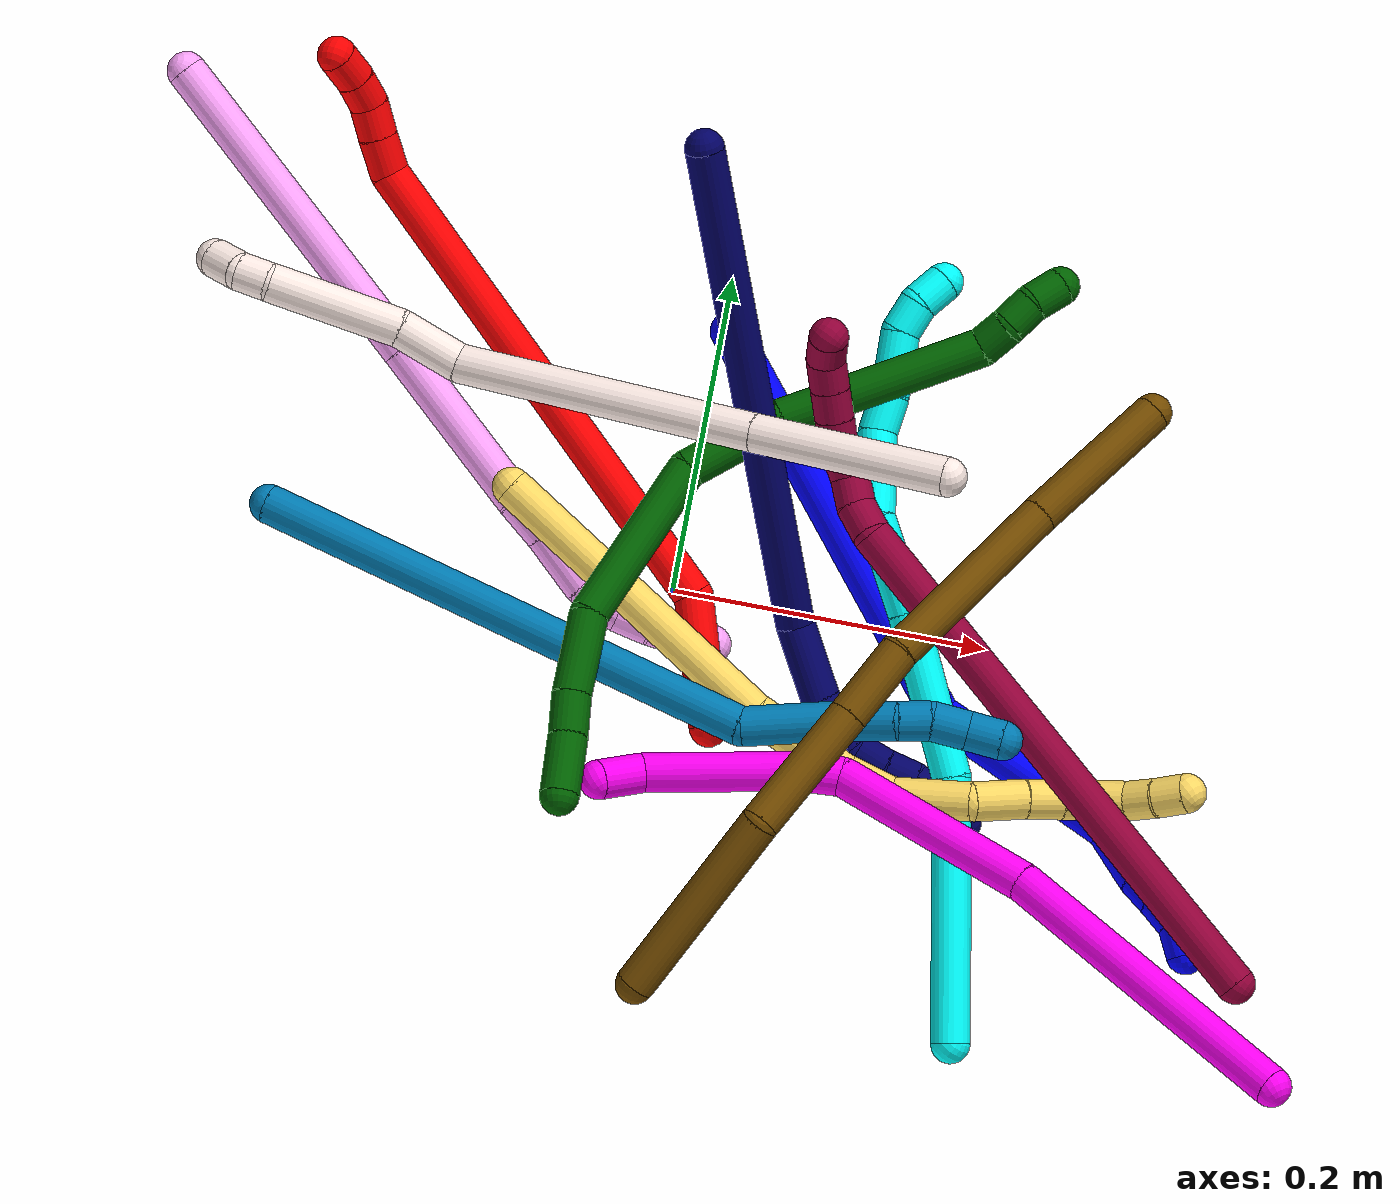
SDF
<sdf version="1.7">
 <world name="default">
  <plugin name="TubeGeneratorPlugin" filename="libtube_generator_plugin.so"/>
  <model name="photoneo_s_sensor">
   <static>1</static>
   <pose>0 0 2 1.57079 1.57079 3.14159</pose>
   <link name="link">
    <inertial><mass>0.1</mass></inertial>
    <sensor name="sensor" type="depth">
     <update_rate>30</update_rate>
     <camera>
      <horizontal_fov>1.22</horizontal_fov>
      <image><width>1920</width><height>1200</height><format>B8G8R8</format></image>
      <clip><near>0.1</near><far>4</far></clip>
      <depth_camera><output>points</output></depth_camera>
     </camera>
     <plugin name="camera_plugin" filename="libgazebo_ros_depth_camera.so">
      <baseline>0.2</baseline>
      <alwaysOn>1</alwaysOn>
      <updateRate>0.0</updateRate>
      <cameraName>camera_ir</cameraName>
      <imageTopicName>/camera/color/image_raw</imageTopicName>
      <cameraInfoTopicName>/camera/color/camera_info</cameraInfoTopicName>
      <depthImageTopicName>/camera/depth/image_raw</depthImageTopicName>
      <depthImageCameraInfoTopicName>/camera/depth/camera_info</depthImageCameraInfoTopicName>
      <pointCloudTopicName>/camera/depth/points</pointCloudTopicName>
      <frameName>fr_optical</frameName>
      <pointCloudCutoff>0.1</pointCloudCutoff>
      <pointCloudCutoffMax>2.0</pointCloudCutoffMax>
      <distortionK1>0</distortionK1>
      <distortionK2>0</distortionK2>
      <distortionK3>0</distortionK3>
      <distortionT1>0</distortionT1>
      <distortionT2>0</distortionT2>
      <CxPrime>0</CxPrime>
      <Cx>0</Cx>
      <Cy>0</Cy>
      <focalLength>0</focalLength>
      <hackBaseline>0</hackBaseline>
     </plugin>
    </sensor>
   </link>
  </model>
  <gravity>0 0 -9.8</gravity>
  <magnetic_field>6e-06 2.3e-05 -4.2e-05</magnetic_field>
  <atmosphere type="adiabatic"/>
  <physics name="default_physics" default="0" type="ode">
   <max_step_size>0.003</max_step_size>
   <real_time_factor>1</real_time_factor>
   <real_time_update_rate>1000</real_time_update_rate>
   <max_contacts>10000</max_contacts>
   <ode>
    <solver>
     <type>quick</type>
     <iters>100</iters>
     <sor>1.3</sor>
     <use_dynamic_moi_rescaling>0</use_dynamic_moi_rescaling>
    </solver>
    <constraints>
     <contact_max_correcting_vel>0</contact_max_correcting_vel>
     <contact_surface_layer>0.001</contact_surface_layer>
     <cfm>0</cfm>
     <erp>0.2</erp>
    </constraints>
   </ode>
  </physics>
  <scene><ambient>0.4 0.4 0.4 1</ambient><background>0.7 0.7 0.7 1</background><shadows>0</shadows></scene>
  <audio><device>default</device></audio>
  <spherical_coordinates>
   <surface_model>EARTH_WGS84</surface_model>
   <latitude_deg>0</latitude_deg>
   <longitude_deg>0</longitude_deg>
   <elevation>0</elevation>
   <heading_deg>0</heading_deg>
  </spherical_coordinates>
  <model name="bin">
   <static>1</static>
   <link name="bottom">
    <collision name="collision-bottom">
     <pose>0 0 -0.01 0 -0 0</pose>
     <geometry><box><size>0.8 0.6 0.02</size></box></geometry>
     <surface>
      <friction><ode><mu>100</mu><mu2>100</mu2></ode></friction>
      <contact><collide_bitmask>65535</collide_bitmask></contact>
     </surface>
    </collision>
   </link>
   <link name="west_wall">
    <collision name="collision-west_wall">
     <pose>-0.41 0 0.1 0 -0 0</pose>
     <geometry><box><size>0.02 0.6 0.2</size></box></geometry>
     <surface>
      <friction><ode><mu>100</mu><mu2>100</mu2></ode></friction>
      <contact><collide_bitmask>65535</collide_bitmask></contact>
     </surface>
    </collision>
   </link>
   <link name="east_wall">
    <collision name="collision-east_wall">
     <pose>0.41 0 0.1 0 -0 0</pose>
     <geometry><box><size>0.02 0.6 0.2</size></box></geometry>
     <surface>
      <friction><ode><mu>100</mu><mu2>100</mu2></ode></friction>
      <contact><collide_bitmask>65535</collide_bitmask></contact>
     </surface>
    </collision>
   </link>
   <link name="south_wall">
    <collision name="collision-south_wall">
     <pose>0 -0.31 0.1 0 -0 0</pose>
     <geometry><box><size>0.8 0.02 0.2</size></box></geometry>
     <surface>
      <friction><ode><mu>100</mu><mu2>100</mu2></ode></friction>
      <contact><collide_bitmask>65535</collide_bitmask></contact>
     </surface>
    </collision>
   </link>
   <link name="north_wall">
    <collision name="collision-north_wall">
     <pose>0 0.31 0.1 0 -0 0</pose>
     <geometry><box><size>0.8 0.02 0.2</size></box></geometry>
     <surface>
      <friction><ode><mu>100</mu><mu2>100</mu2></ode></friction>
      <contact><collide_bitmask>65535</collide_bitmask></contact>
     </surface>
    </collision>
   </link>
  </model>
  <model name="1">
   <static>0</static>
   <link name="1">
    <collision name="collision-cylinder-e_1_1_4">
     <pose>0.085048 -0.096403 0.048234 1.10688 0.667979 0.422379</pose>
     <geometry><cylinder><radius>0.0125</radius><length>0.274613</length></cylinder></geometry>
     <surface>
      <friction><ode><mu>1.16</mu><mu2>1.16</mu2><slip1>0</slip1><slip2>0</slip2></ode></friction>
      <contact><ode><kp>1e+06</kp><kd>1</kd><max_vel>0</max_vel><min_depth>0.001</min_depth></ode></contact>
     </surface>
    </collision>
    <visual name="visual-cylinder-e_1_1_4">
     <pose>0.085048 -0.096403 0.048234 1.10688 0.667979 0.422379</pose>
     <geometry><cylinder><radius>0.0125</radius><length>0.274613</length></cylinder></geometry>
     <material><ambient>0 0 1 1</ambient></material>
    </visual>
    <collision name="collision-cylinder-e_2_4_5">
     <pose>0.206422 -0.219303 0.141283 0.53396 0.609203 0.171553</pose>
     <geometry><cylinder><radius>0.0125</radius><length>0.126967</length></cylinder></geometry>
     <surface>
      <friction><ode><mu>1.16</mu><mu2>1.16</mu2><slip1>0</slip1><slip2>0</slip2></ode></friction>
      <contact><ode><kp>1e+06</kp><kd>1</kd><max_vel>0</max_vel><min_depth>0.001</min_depth></ode></contact>
     </surface>
    </collision>
    <visual name="visual-cylinder-e_2_4_5">
     <pose>0.206422 -0.219303 0.141283 0.53396 0.609203 0.171553</pose>
     <geometry><cylinder><radius>0.0125</radius><length>0.126967</length></cylinder></geometry>
     <material><ambient>0 0 1 1</ambient></material>
    </visual>
    <collision name="collision-cylinder-e_3_5_6">
     <pose>0.251168 -0.260053 0.194816 1.02189 0.466813 0.264994</pose>
     <geometry><cylinder><radius>0.0125</radius><length>0.037418</length></cylinder></geometry>
     <surface>
      <friction><ode><mu>1.16</mu><mu2>1.16</mu2><slip1>0</slip1><slip2>0</slip2></ode></friction>
      <contact><ode><kp>1e+06</kp><kd>1</kd><max_vel>0</max_vel><min_depth>0.001</min_depth></ode></contact>
     </surface>
    </collision>
    <visual name="visual-cylinder-e_3_5_6">
     <pose>0.251168 -0.260053 0.194816 1.02189 0.466813 0.264994</pose>
     <geometry><cylinder><radius>0.0125</radius><length>0.037418</length></cylinder></geometry>
     <material><ambient>0 0 1 1</ambient></material>
    </visual>
    <collision name="collision-cylinder-e_4_6_7">
     <pose>0.260927 -0.282239 0.210111 0.878471 0.129265 0.060801</pose>
     <geometry><cylinder><radius>0.0125</radius><length>0.020783</length></cylinder></geometry>
     <surface>
      <friction><ode><mu>1.16</mu><mu2>1.16</mu2><slip1>0</slip1><slip2>0</slip2></ode></friction>
      <contact><ode><kp>1e+06</kp><kd>1</kd><max_vel>0</max_vel><min_depth>0.001</min_depth></ode></contact>
     </surface>
    </collision>
    <visual name="visual-cylinder-e_4_6_7">
     <pose>0.260927 -0.282239 0.210111 0.878471 0.129265 0.060801</pose>
     <geometry><cylinder><radius>0.0125</radius><length>0.020783</length></cylinder></geometry>
     <material><ambient>0 0 1 1</ambient></material>
    </visual>
    <collision name="collision-cylinder-e_5_7_8">
     <pose>0.264656 -0.297902 0.222736 0.907081 0.23877 0.116807</pose>
     <geometry><cylinder><radius>0.0125</radius><length>0.020203</length></cylinder></geometry>
     <surface>
      <friction><ode><mu>1.16</mu><mu2>1.16</mu2><slip1>0</slip1><slip2>0</slip2></ode></friction>
      <contact><ode><kp>1e+06</kp><kd>1</kd><max_vel>0</max_vel><min_depth>0.001</min_depth></ode></contact>
     </surface>
    </collision>
    <visual name="visual-cylinder-e_5_7_8">
     <pose>0.264656 -0.297902 0.222736 0.907081 0.23877 0.116807</pose>
     <geometry><cylinder><radius>0.0125</radius><length>0.020203</length></cylinder></geometry>
     <material><ambient>0 0 1 1</ambient></material>
    </visual>
    <collision name="collision-cylinder-e_6_8_2">
     <pose>0.272279 -0.313984 0.230523 1.36524 0.550362 0.451275</pose>
     <geometry><cylinder><radius>0.0125</radius><length>0.020015</length></cylinder></geometry>
     <surface>
      <friction><ode><mu>1.16</mu><mu2>1.16</mu2><slip1>0</slip1><slip2>0</slip2></ode></friction>
      <contact><ode><kp>1e+06</kp><kd>1</kd><max_vel>0</max_vel><min_depth>0.001</min_depth></ode></contact>
     </surface>
    </collision>
    <visual name="visual-cylinder-e_6_8_2">
     <pose>0.272279 -0.313984 0.230523 1.36524 0.550362 0.451275</pose>
     <geometry><cylinder><radius>0.0125</radius><length>0.020015</length></cylinder></geometry>
     <material><ambient>0 0 1 1</ambient></material>
    </visual>
    <collision name="collision-sphere-2">
     <pose>0.277513 -0.322334 0.232264 0 -0 0</pose>
     <geometry><sphere><radius>0.0125</radius></sphere></geometry>
     <surface>
      <friction><ode><mu>1.16</mu><mu2>1.16</mu2><slip1>0</slip1><slip2>0</slip2></ode></friction>
      <contact><ode><kp>1e+06</kp><kd>1</kd><max_vel>0</max_vel><min_depth>0.001</min_depth></ode></contact>
     </surface>
    </collision>
    <visual name="visual-sphere-2">
     <pose>0.277513 -0.322334 0.232264 0 -0 0</pose>
     <geometry><sphere><radius>0.0125</radius></sphere></geometry>
     <material><ambient>0 0 1 1</ambient></material>
    </visual>
    <collision name="collision-sphere-4">
     <pose>0.170095 -0.192805 0.096467 0 -0 0</pose>
     <geometry><sphere><radius>0.0125</radius></sphere></geometry>
     <surface>
      <friction><ode><mu>1.16</mu><mu2>1.16</mu2><slip1>0</slip1><slip2>0</slip2></ode></friction>
      <contact><ode><kp>1e+06</kp><kd>1</kd><max_vel>0</max_vel><min_depth>0.001</min_depth></ode></contact>
     </surface>
    </collision>
    <visual name="visual-sphere-4">
     <pose>0.170095 -0.192805 0.096467 0 -0 0</pose>
     <geometry><sphere><radius>0.0125</radius></sphere></geometry>
     <material><ambient>0 0 1 1</ambient></material>
    </visual>
    <collision name="collision-sphere-1">
     <geometry><sphere><radius>0.0125</radius></sphere></geometry>
     <surface>
      <friction><ode><mu>1.16</mu><mu2>1.16</mu2><slip1>0</slip1><slip2>0</slip2></ode></friction>
      <contact><ode><kp>1e+06</kp><kd>1</kd><max_vel>0</max_vel><min_depth>0.001</min_depth></ode></contact>
     </surface>
    </collision>
    <visual name="visual-sphere-1">
     <geometry><sphere><radius>0.0125</radius></sphere></geometry>
     <material><ambient>0 0 1 1</ambient></material>
    </visual>
    <collision name="collision-sphere-8">
     <pose>0.267045 -0.305633 0.228782 0 -0 0</pose>
     <geometry><sphere><radius>0.0125</radius></sphere></geometry>
     <surface>
      <friction><ode><mu>1.16</mu><mu2>1.16</mu2><slip1>0</slip1><slip2>0</slip2></ode></friction>
      <contact><ode><kp>1e+06</kp><kd>1</kd><max_vel>0</max_vel><min_depth>0.001</min_depth></ode></contact>
     </surface>
    </collision>
    <visual name="visual-sphere-8">
     <pose>0.267045 -0.305633 0.228782 0 -0 0</pose>
     <geometry><sphere><radius>0.0125</radius></sphere></geometry>
     <material><ambient>0 0 1 1</ambient></material>
    </visual>
    <collision name="collision-sphere-5">
     <pose>0.242748 -0.2458 0.186099 0 -0 0</pose>
     <geometry><sphere><radius>0.0125</radius></sphere></geometry>
     <surface>
      <friction><ode><mu>1.16</mu><mu2>1.16</mu2><slip1>0</slip1><slip2>0</slip2></ode></friction>
      <contact><ode><kp>1e+06</kp><kd>1</kd><max_vel>0</max_vel><min_depth>0.001</min_depth></ode></contact>
     </surface>
    </collision>
    <visual name="visual-sphere-5">
     <pose>0.242748 -0.2458 0.186099 0 -0 0</pose>
     <geometry><sphere><radius>0.0125</radius></sphere></geometry>
     <material><ambient>0 0 1 1</ambient></material>
    </visual>
    <collision name="collision-sphere-6">
     <pose>0.259588 -0.274306 0.203533 0 -0 0</pose>
     <geometry><sphere><radius>0.0125</radius></sphere></geometry>
     <surface>
      <friction><ode><mu>1.16</mu><mu2>1.16</mu2><slip1>0</slip1><slip2>0</slip2></ode></friction>
      <contact><ode><kp>1e+06</kp><kd>1</kd><max_vel>0</max_vel><min_depth>0.001</min_depth></ode></contact>
     </surface>
    </collision>
    <visual name="visual-sphere-6">
     <pose>0.259588 -0.274306 0.203533 0 -0 0</pose>
     <geometry><sphere><radius>0.0125</radius></sphere></geometry>
     <material><ambient>0 0 1 1</ambient></material>
    </visual>
    <collision name="collision-sphere-7">
     <pose>0.262267 -0.290171 0.216689 0 -0 0</pose>
     <geometry><sphere><radius>0.0125</radius></sphere></geometry>
     <surface>
      <friction><ode><mu>1.16</mu><mu2>1.16</mu2><slip1>0</slip1><slip2>0</slip2></ode></friction>
      <contact><ode><kp>1e+06</kp><kd>1</kd><max_vel>0</max_vel><min_depth>0.001</min_depth></ode></contact>
     </surface>
    </collision>
    <visual name="visual-sphere-7">
     <pose>0.262267 -0.290171 0.216689 0 -0 0</pose>
     <geometry><sphere><radius>0.0125</radius></sphere></geometry>
     <material><ambient>0 0 1 1</ambient></material>
    </visual>
    <inertial>
     <pose>0.150364 -0.164434 0.103909 0 -0 0</pose>
     <mass>0.5</mass>
     <inertia>
      <ixx>0.002002</ixx>
      <ixy>0</ixy>
      <ixz>0</ixz>
      <iyy>0.001827</iyy>
      <iyz>0</iyz>
      <izz>0.000139</izz>
     </inertia>
    </inertial>
   </link>
   <pose>0.004342 0.166831 0.01149 -1.00327 0.900172 -0.798296</pose>
  </model>
  <model name="2">
   <static>0</static>
   <link name="2">
    <collision name="collision-cylinder-e_1_1_4">
     <pose>-0.015242 0.012703 0.036487 -0.335036 -0.375768 0.06428</pose>
     <geometry><cylinder><radius>0.0125</radius><length>0.083067</length></cylinder></geometry>
     <surface>
      <friction><ode><mu>1.16</mu><mu2>1.16</mu2><slip1>0</slip1><slip2>0</slip2></ode></friction>
      <contact><ode><kp>1e+06</kp><kd>1</kd><max_vel>0</max_vel><min_depth>0.001</min_depth></ode></contact>
     </surface>
    </collision>
    <visual name="visual-cylinder-e_1_1_4">
     <pose>-0.015242 0.012703 0.036487 -0.335036 -0.375768 0.06428</pose>
     <geometry><cylinder><radius>0.0125</radius><length>0.083067</length></cylinder></geometry>
     <material><ambient>1 0 0 1</ambient></material>
    </visual>
    <collision name="collision-cylinder-e_2_4_5">
     <pose>-0.111614 0.135171 0.163705 -0.880046 -0.51784 0.248121</pose>
     <geometry><cylinder><radius>0.0125</radius><length>0.327793</length></cylinder></geometry>
     <surface>
      <friction><ode><mu>1.16</mu><mu2>1.16</mu2><slip1>0</slip1><slip2>0</slip2></ode></friction>
      <contact><ode><kp>1e+06</kp><kd>1</kd><max_vel>0</max_vel><min_depth>0.001</min_depth></ode></contact>
     </surface>
    </collision>
    <visual name="visual-cylinder-e_2_4_5">
     <pose>-0.111614 0.135171 0.163705 -0.880046 -0.51784 0.248121</pose>
     <geometry><cylinder><radius>0.0125</radius><length>0.327793</length></cylinder></geometry>
     <material><ambient>1 0 0 1</ambient></material>
    </visual>
    <collision name="collision-cylinder-e_3_5_6">
     <pose>-0.202595 0.248078 0.262413 -0.375416 -0.854585 0.172552</pose>
     <geometry><cylinder><radius>0.0125</radius><length>0.02612</length></cylinder></geometry>
     <surface>
      <friction><ode><mu>1.16</mu><mu2>1.16</mu2><slip1>0</slip1><slip2>0</slip2></ode></friction>
      <contact><ode><kp>1e+06</kp><kd>1</kd><max_vel>0</max_vel><min_depth>0.001</min_depth></ode></contact>
     </surface>
    </collision>
    <visual name="visual-cylinder-e_3_5_6">
     <pose>-0.202595 0.248078 0.262413 -0.375416 -0.854585 0.172552</pose>
     <geometry><cylinder><radius>0.0125</radius><length>0.02612</length></cylinder></geometry>
     <material><ambient>1 0 0 1</ambient></material>
    </visual>
    <collision name="collision-cylinder-e_4_6_7">
     <pose>-0.220658 0.253515 0.277298 -0.320579 -0.845598 0.145232</pose>
     <geometry><cylinder><radius>0.0125</radius><length>0.021947</length></cylinder></geometry>
     <surface>
      <friction><ode><mu>1.16</mu><mu2>1.16</mu2><slip1>0</slip1><slip2>0</slip2></ode></friction>
      <contact><ode><kp>1e+06</kp><kd>1</kd><max_vel>0</max_vel><min_depth>0.001</min_depth></ode></contact>
     </surface>
    </collision>
    <visual name="visual-cylinder-e_4_6_7">
     <pose>-0.220658 0.253515 0.277298 -0.320579 -0.845598 0.145232</pose>
     <geometry><cylinder><radius>0.0125</radius><length>0.021947</length></cylinder></geometry>
     <material><ambient>1 0 0 1</ambient></material>
    </visual>
    <collision name="collision-cylinder-e_5_7_8">
     <pose>-0.238219 0.25802 0.287671 -0.567887 -1.1565 0.376429</pose>
     <geometry><cylinder><radius>0.0125</radius><length>0.020424</length></cylinder></geometry>
     <surface>
      <friction><ode><mu>1.16</mu><mu2>1.16</mu2><slip1>0</slip1><slip2>0</slip2></ode></friction>
      <contact><ode><kp>1e+06</kp><kd>1</kd><max_vel>0</max_vel><min_depth>0.001</min_depth></ode></contact>
     </surface>
    </collision>
    <visual name="visual-cylinder-e_5_7_8">
     <pose>-0.238219 0.25802 0.287671 -0.567887 -1.1565 0.376429</pose>
     <geometry><cylinder><radius>0.0125</radius><length>0.020424</length></cylinder></geometry>
     <material><ambient>1 0 0 1</ambient></material>
    </visual>
    <collision name="collision-cylinder-e_6_8_2">
     <pose>-0.257225 0.263085 0.293412 -0.897648 -1.20949 0.642631</pose>
     <geometry><cylinder><radius>0.0125</radius><length>0.020648</length></cylinder></geometry>
     <surface>
      <friction><ode><mu>1.16</mu><mu2>1.16</mu2><slip1>0</slip1><slip2>0</slip2></ode></friction>
      <contact><ode><kp>1e+06</kp><kd>1</kd><max_vel>0</max_vel><min_depth>0.001</min_depth></ode></contact>
     </surface>
    </collision>
    <visual name="visual-cylinder-e_6_8_2">
     <pose>-0.257225 0.263085 0.293412 -0.897648 -1.20949 0.642631</pose>
     <geometry><cylinder><radius>0.0125</radius><length>0.020648</length></cylinder></geometry>
     <material><ambient>1 0 0 1</ambient></material>
    </visual>
    <collision name="collision-sphere-2">
     <pose>-0.266882 0.265938 0.295687 0 -0 0</pose>
     <geometry><sphere><radius>0.0125</radius></sphere></geometry>
     <surface>
      <friction><ode><mu>1.16</mu><mu2>1.16</mu2><slip1>0</slip1><slip2>0</slip2></ode></friction>
      <contact><ode><kp>1e+06</kp><kd>1</kd><max_vel>0</max_vel><min_depth>0.001</min_depth></ode></contact>
     </surface>
    </collision>
    <visual name="visual-sphere-2">
     <pose>-0.266882 0.265938 0.295687 0 -0 0</pose>
     <geometry><sphere><radius>0.0125</radius></sphere></geometry>
     <material><ambient>1 0 0 1</ambient></material>
    </visual>
    <collision name="collision-sphere-4">
     <pose>-0.030484 0.025407 0.072975 0 -0 0</pose>
     <geometry><sphere><radius>0.0125</radius></sphere></geometry>
     <surface>
      <friction><ode><mu>1.16</mu><mu2>1.16</mu2><slip1>0</slip1><slip2>0</slip2></ode></friction>
      <contact><ode><kp>1e+06</kp><kd>1</kd><max_vel>0</max_vel><min_depth>0.001</min_depth></ode></contact>
     </surface>
    </collision>
    <visual name="visual-sphere-4">
     <pose>-0.030484 0.025407 0.072975 0 -0 0</pose>
     <geometry><sphere><radius>0.0125</radius></sphere></geometry>
     <material><ambient>1 0 0 1</ambient></material>
    </visual>
    <collision name="collision-sphere-1">
     <geometry><sphere><radius>0.0125</radius></sphere></geometry>
     <surface>
      <friction><ode><mu>1.16</mu><mu2>1.16</mu2><slip1>0</slip1><slip2>0</slip2></ode></friction>
      <contact><ode><kp>1e+06</kp><kd>1</kd><max_vel>0</max_vel><min_depth>0.001</min_depth></ode></contact>
     </surface>
    </collision>
    <visual name="visual-sphere-1">
     <geometry><sphere><radius>0.0125</radius></sphere></geometry>
     <material><ambient>1 0 0 1</ambient></material>
    </visual>
    <collision name="collision-sphere-8">
     <pose>-0.247567 0.260231 0.291137 0 -0 0</pose>
     <geometry><sphere><radius>0.0125</radius></sphere></geometry>
     <surface>
      <friction><ode><mu>1.16</mu><mu2>1.16</mu2><slip1>0</slip1><slip2>0</slip2></ode></friction>
      <contact><ode><kp>1e+06</kp><kd>1</kd><max_vel>0</max_vel><min_depth>0.001</min_depth></ode></contact>
     </surface>
    </collision>
    <visual name="visual-sphere-8">
     <pose>-0.247567 0.260231 0.291137 0 -0 0</pose>
     <geometry><sphere><radius>0.0125</radius></sphere></geometry>
     <material><ambient>1 0 0 1</ambient></material>
    </visual>
    <collision name="collision-sphere-5">
     <pose>-0.192743 0.244934 0.254436 0 -0 0</pose>
     <geometry><sphere><radius>0.0125</radius></sphere></geometry>
     <surface>
      <friction><ode><mu>1.16</mu><mu2>1.16</mu2><slip1>0</slip1><slip2>0</slip2></ode></friction>
      <contact><ode><kp>1e+06</kp><kd>1</kd><max_vel>0</max_vel><min_depth>0.001</min_depth></ode></contact>
     </surface>
    </collision>
    <visual name="visual-sphere-5">
     <pose>-0.192743 0.244934 0.254436 0 -0 0</pose>
     <geometry><sphere><radius>0.0125</radius></sphere></geometry>
     <material><ambient>1 0 0 1</ambient></material>
    </visual>
    <collision name="collision-sphere-6">
     <pose>-0.212446 0.251222 0.27039 0 -0 0</pose>
     <geometry><sphere><radius>0.0125</radius></sphere></geometry>
     <surface>
      <friction><ode><mu>1.16</mu><mu2>1.16</mu2><slip1>0</slip1><slip2>0</slip2></ode></friction>
      <contact><ode><kp>1e+06</kp><kd>1</kd><max_vel>0</max_vel><min_depth>0.001</min_depth></ode></contact>
     </surface>
    </collision>
    <visual name="visual-sphere-6">
     <pose>-0.212446 0.251222 0.27039 0 -0 0</pose>
     <geometry><sphere><radius>0.0125</radius></sphere></geometry>
     <material><ambient>1 0 0 1</ambient></material>
    </visual>
    <collision name="collision-sphere-7">
     <pose>-0.22887 0.255809 0.284206 0 -0 0</pose>
     <geometry><sphere><radius>0.0125</radius></sphere></geometry>
     <surface>
      <friction><ode><mu>1.16</mu><mu2>1.16</mu2><slip1>0</slip1><slip2>0</slip2></ode></friction>
      <contact><ode><kp>1e+06</kp><kd>1</kd><max_vel>0</max_vel><min_depth>0.001</min_depth></ode></contact>
     </surface>
    </collision>
    <visual name="visual-sphere-7">
     <pose>-0.22887 0.255809 0.284206 0 -0 0</pose>
     <geometry><sphere><radius>0.0125</radius></sphere></geometry>
     <material><ambient>1 0 0 1</ambient></material>
    </visual>
    <inertial>
     <pose>-0.116328 0.136218 0.163133 0 -0 0</pose>
     <mass>0.5</mass>
     <inertia>
      <ixx>0.003146</ixx>
      <ixy>0</ixy>
      <ixz>0</ixz>
      <iyy>0.002806</iyy>
      <iyz>0</iyz>
      <izz>-0.000485</izz>
     </inertia>
    </inertial>
   </link>
   <pose>0.038005 -0.079601 0.042766 -2.17823 0.986344 -0.685444</pose>
  </model>
  <model name="3">
   <static>0</static>
   <link name="3">
    <collision name="collision-cylinder-e_1_1_4">
     <pose>0.025781 0.053803 0.057916 -0.748597 0.315257 -0.124712</pose>
     <geometry><cylinder><radius>0.0125</radius><length>0.166297</length></cylinder></geometry>
     <surface>
      <friction><ode><mu>1.16</mu><mu2>1.16</mu2><slip1>0</slip1><slip2>0</slip2></ode></friction>
      <contact><ode><kp>1e+06</kp><kd>1</kd><max_vel>0</max_vel><min_depth>0.001</min_depth></ode></contact>
     </surface>
    </collision>
    <visual name="visual-cylinder-e_1_1_4">
     <pose>0.025781 0.053803 0.057916 -0.748597 0.315257 -0.124712</pose>
     <geometry><cylinder><radius>0.0125</radius><length>0.166297</length></cylinder></geometry>
     <material><ambient>0.003922 1 0.996078 1</ambient></material>
    </visual>
    <collision name="collision-cylinder-e_2_4_5">
     <pose>0.061353 0.151667 0.144162 -0.999385 0.184771 -0.101069</pose>
     <geometry><cylinder><radius>0.0125</radius><length>0.106579</length></cylinder></geometry>
     <surface>
      <friction><ode><mu>1.16</mu><mu2>1.16</mu2><slip1>0</slip1><slip2>0</slip2></ode></friction>
      <contact><ode><kp>1e+06</kp><kd>1</kd><max_vel>0</max_vel><min_depth>0.001</min_depth></ode></contact>
     </surface>
    </collision>
    <visual name="visual-cylinder-e_2_4_5">
     <pose>0.061353 0.151667 0.144162 -0.999385 0.184771 -0.101069</pose>
     <geometry><cylinder><radius>0.0125</radius><length>0.106579</length></cylinder></geometry>
     <material><ambient>0.003922 1 0.996078 1</ambient></material>
    </visual>
    <collision name="collision-cylinder-e_3_5_6">
     <pose>0.073161 0.211985 0.182049 -1.03932 0.106577 -0.061012</pose>
     <geometry><cylinder><radius>0.0125</radius><length>0.037933</length></cylinder></geometry>
     <surface>
      <friction><ode><mu>1.16</mu><mu2>1.16</mu2><slip1>0</slip1><slip2>0</slip2></ode></friction>
      <contact><ode><kp>1e+06</kp><kd>1</kd><max_vel>0</max_vel><min_depth>0.001</min_depth></ode></contact>
     </surface>
    </collision>
    <visual name="visual-cylinder-e_3_5_6">
     <pose>0.073161 0.211985 0.182049 -1.03932 0.106577 -0.061012</pose>
     <geometry><cylinder><radius>0.0125</radius><length>0.037933</length></cylinder></geometry>
     <material><ambient>0.003922 1 0.996078 1</ambient></material>
    </visual>
    <collision name="collision-cylinder-e_4_6_7">
     <pose>0.076541 0.239226 0.198073 -1.03873 0.106517 -0.060937</pose>
     <geometry><cylinder><radius>0.0125</radius><length>0.025636</length></cylinder></geometry>
     <surface>
      <friction><ode><mu>1.16</mu><mu2>1.16</mu2><slip1>0</slip1><slip2>0</slip2></ode></friction>
      <contact><ode><kp>1e+06</kp><kd>1</kd><max_vel>0</max_vel><min_depth>0.001</min_depth></ode></contact>
     </surface>
    </collision>
    <visual name="visual-cylinder-e_4_6_7">
     <pose>0.076541 0.239226 0.198073 -1.03873 0.106517 -0.060937</pose>
     <geometry><cylinder><radius>0.0125</radius><length>0.025636</length></cylinder></geometry>
     <material><ambient>0.003922 1 0.996078 1</ambient></material>
    </visual>
    <collision name="collision-cylinder-e_5_7_8">
     <pose>0.09151 0.267252 0.221883 -0.776621 0.51014 -0.212532</pose>
     <geometry><cylinder><radius>0.0125</radius><length>0.055728</length></cylinder></geometry>
     <surface>
      <friction><ode><mu>1.16</mu><mu2>1.16</mu2><slip1>0</slip1><slip2>0</slip2></ode></friction>
      <contact><ode><kp>1e+06</kp><kd>1</kd><max_vel>0</max_vel><min_depth>0.001</min_depth></ode></contact>
     </surface>
    </collision>
    <visual name="visual-cylinder-e_5_7_8">
     <pose>0.09151 0.267252 0.221883 -0.776621 0.51014 -0.212532</pose>
     <geometry><cylinder><radius>0.0125</radius><length>0.055728</length></cylinder></geometry>
     <material><ambient>0.003922 1 0.996078 1</ambient></material>
    </visual>
    <collision name="collision-cylinder-e_6_8_9">
     <pose>0.108845 0.288999 0.249941 -0.413748 0.308571 -0.065258</pose>
     <geometry><cylinder><radius>0.0125</radius><length>0.024561</length></cylinder></geometry>
     <surface>
      <friction><ode><mu>1.16</mu><mu2>1.16</mu2><slip1>0</slip1><slip2>0</slip2></ode></friction>
      <contact><ode><kp>1e+06</kp><kd>1</kd><max_vel>0</max_vel><min_depth>0.001</min_depth></ode></contact>
     </surface>
    </collision>
    <visual name="visual-cylinder-e_6_8_9">
     <pose>0.108845 0.288999 0.249941 -0.413748 0.308571 -0.065258</pose>
     <geometry><cylinder><radius>0.0125</radius><length>0.024561</length></cylinder></geometry>
     <material><ambient>0.003922 1 0.996078 1</ambient></material>
    </visual>
    <collision name="collision-cylinder-e_7_9_10">
     <pose>0.117328 0.30428 0.277378 -0.563961 0.235746 -0.068587</pose>
     <geometry><cylinder><radius>0.0125</radius><length>0.040702</length></cylinder></geometry>
     <surface>
      <friction><ode><mu>1.16</mu><mu2>1.16</mu2><slip1>0</slip1><slip2>0</slip2></ode></friction>
      <contact><ode><kp>1e+06</kp><kd>1</kd><max_vel>0</max_vel><min_depth>0.001</min_depth></ode></contact>
     </surface>
    </collision>
    <visual name="visual-cylinder-e_7_9_10">
     <pose>0.117328 0.30428 0.277378 -0.563961 0.235746 -0.068587</pose>
     <geometry><cylinder><radius>0.0125</radius><length>0.040702</length></cylinder></geometry>
     <material><ambient>0.003922 1 0.996078 1</ambient></material>
    </visual>
    <collision name="collision-cylinder-e_8_10_11">
     <pose>0.124964 0.316402 0.304203 -0.151695 0.274886 -0.021021</pose>
     <geometry><cylinder><radius>0.0125</radius><length>0.021235</length></cylinder></geometry>
     <surface>
      <friction><ode><mu>1.16</mu><mu2>1.16</mu2><slip1>0</slip1><slip2>0</slip2></ode></friction>
      <contact><ode><kp>1e+06</kp><kd>1</kd><max_vel>0</max_vel><min_depth>0.001</min_depth></ode></contact>
     </surface>
    </collision>
    <visual name="visual-cylinder-e_8_10_11">
     <pose>0.124964 0.316402 0.304203 -0.151695 0.274886 -0.021021</pose>
     <geometry><cylinder><radius>0.0125</radius><length>0.021235</length></cylinder></geometry>
     <material><ambient>0.003922 1 0.996078 1</ambient></material>
    </visual>
    <collision name="collision-cylinder-e_9_11_2">
     <pose>0.133249 0.316374 0.323363 0.171795 0.53137 0.046855</pose>
     <geometry><cylinder><radius>0.0125</radius><length>0.021329</length></cylinder></geometry>
     <surface>
      <friction><ode><mu>1.16</mu><mu2>1.16</mu2><slip1>0</slip1><slip2>0</slip2></ode></friction>
      <contact><ode><kp>1e+06</kp><kd>1</kd><max_vel>0</max_vel><min_depth>0.001</min_depth></ode></contact>
     </surface>
    </collision>
    <visual name="visual-cylinder-e_9_11_2">
     <pose>0.133249 0.316374 0.323363 0.171795 0.53137 0.046855</pose>
     <geometry><cylinder><radius>0.0125</radius><length>0.021329</length></cylinder></geometry>
     <material><ambient>0.003922 1 0.996078 1</ambient></material>
    </visual>
    <collision name="collision-sphere-2">
     <pose>0.138653 0.314802 0.332422 0 -0 0</pose>
     <geometry><sphere><radius>0.0125</radius></sphere></geometry>
     <surface>
      <friction><ode><mu>1.16</mu><mu2>1.16</mu2><slip1>0</slip1><slip2>0</slip2></ode></friction>
      <contact><ode><kp>1e+06</kp><kd>1</kd><max_vel>0</max_vel><min_depth>0.001</min_depth></ode></contact>
     </surface>
    </collision>
    <visual name="visual-sphere-2">
     <pose>0.138653 0.314802 0.332422 0 -0 0</pose>
     <geometry><sphere><radius>0.0125</radius></sphere></geometry>
     <material><ambient>0.003922 1 0.996078 1</ambient></material>
    </visual>
    <collision name="collision-sphere-11">
     <pose>0.127845 0.317946 0.314304 0 -0 0</pose>
     <geometry><sphere><radius>0.0125</radius></sphere></geometry>
     <surface>
      <friction><ode><mu>1.16</mu><mu2>1.16</mu2><slip1>0</slip1><slip2>0</slip2></ode></friction>
      <contact><ode><kp>1e+06</kp><kd>1</kd><max_vel>0</max_vel><min_depth>0.001</min_depth></ode></contact>
     </surface>
    </collision>
    <visual name="visual-sphere-11">
     <pose>0.127845 0.317946 0.314304 0 -0 0</pose>
     <geometry><sphere><radius>0.0125</radius></sphere></geometry>
     <material><ambient>0.003922 1 0.996078 1</ambient></material>
    </visual>
    <collision name="collision-sphere-10">
     <pose>0.122082 0.314858 0.294101 0 -0 0</pose>
     <geometry><sphere><radius>0.0125</radius></sphere></geometry>
     <surface>
      <friction><ode><mu>1.16</mu><mu2>1.16</mu2><slip1>0</slip1><slip2>0</slip2></ode></friction>
      <contact><ode><kp>1e+06</kp><kd>1</kd><max_vel>0</max_vel><min_depth>0.001</min_depth></ode></contact>
     </surface>
    </collision>
    <visual name="visual-sphere-10">
     <pose>0.122082 0.314858 0.294101 0 -0 0</pose>
     <geometry><sphere><radius>0.0125</radius></sphere></geometry>
     <material><ambient>0.003922 1 0.996078 1</ambient></material>
    </visual>
    <collision name="collision-sphere-9">
     <pose>0.112575 0.293703 0.260654 0 -0 0</pose>
     <geometry><sphere><radius>0.0125</radius></sphere></geometry>
     <surface>
      <friction><ode><mu>1.16</mu><mu2>1.16</mu2><slip1>0</slip1><slip2>0</slip2></ode></friction>
      <contact><ode><kp>1e+06</kp><kd>1</kd><max_vel>0</max_vel><min_depth>0.001</min_depth></ode></contact>
     </surface>
    </collision>
    <visual name="visual-sphere-9">
     <pose>0.112575 0.293703 0.260654 0 -0 0</pose>
     <geometry><sphere><radius>0.0125</radius></sphere></geometry>
     <material><ambient>0.003922 1 0.996078 1</ambient></material>
    </visual>
    <collision name="collision-sphere-4">
     <pose>0.051562 0.107606 0.115832 0 -0 0</pose>
     <geometry><sphere><radius>0.0125</radius></sphere></geometry>
     <surface>
      <friction><ode><mu>1.16</mu><mu2>1.16</mu2><slip1>0</slip1><slip2>0</slip2></ode></friction>
      <contact><ode><kp>1e+06</kp><kd>1</kd><max_vel>0</max_vel><min_depth>0.001</min_depth></ode></contact>
     </surface>
    </collision>
    <visual name="visual-sphere-4">
     <pose>0.051562 0.107606 0.115832 0 -0 0</pose>
     <geometry><sphere><radius>0.0125</radius></sphere></geometry>
     <material><ambient>0.003922 1 0.996078 1</ambient></material>
    </visual>
    <collision name="collision-sphere-1">
     <geometry><sphere><radius>0.0125</radius></sphere></geometry>
     <surface>
      <friction><ode><mu>1.16</mu><mu2>1.16</mu2><slip1>0</slip1><slip2>0</slip2></ode></friction>
      <contact><ode><kp>1e+06</kp><kd>1</kd><max_vel>0</max_vel><min_depth>0.001</min_depth></ode></contact>
     </surface>
    </collision>
    <visual name="visual-sphere-1">
     <geometry><sphere><radius>0.0125</radius></sphere></geometry>
     <material><ambient>0.003922 1 0.996078 1</ambient></material>
    </visual>
    <collision name="collision-sphere-8">
     <pose>0.105116 0.284294 0.239227 0 -0 0</pose>
     <geometry><sphere><radius>0.0125</radius></sphere></geometry>
     <surface>
      <friction><ode><mu>1.16</mu><mu2>1.16</mu2><slip1>0</slip1><slip2>0</slip2></ode></friction>
      <contact><ode><kp>1e+06</kp><kd>1</kd><max_vel>0</max_vel><min_depth>0.001</min_depth></ode></contact>
     </surface>
    </collision>
    <visual name="visual-sphere-8">
     <pose>0.105116 0.284294 0.239227 0 -0 0</pose>
     <geometry><sphere><radius>0.0125</radius></sphere></geometry>
     <material><ambient>0.003922 1 0.996078 1</ambient></material>
    </visual>
    <collision name="collision-sphere-5">
     <pose>0.071143 0.195727 0.172491 0 -0 0</pose>
     <geometry><sphere><radius>0.0125</radius></sphere></geometry>
     <surface>
      <friction><ode><mu>1.16</mu><mu2>1.16</mu2><slip1>0</slip1><slip2>0</slip2></ode></friction>
      <contact><ode><kp>1e+06</kp><kd>1</kd><max_vel>0</max_vel><min_depth>0.001</min_depth></ode></contact>
     </surface>
    </collision>
    <visual name="visual-sphere-5">
     <pose>0.071143 0.195727 0.172491 0 -0 0</pose>
     <geometry><sphere><radius>0.0125</radius></sphere></geometry>
     <material><ambient>0.003922 1 0.996078 1</ambient></material>
    </visual>
    <collision name="collision-sphere-6">
     <pose>0.075178 0.228242 0.191607 0 -0 0</pose>
     <geometry><sphere><radius>0.0125</radius></sphere></geometry>
     <surface>
      <friction><ode><mu>1.16</mu><mu2>1.16</mu2><slip1>0</slip1><slip2>0</slip2></ode></friction>
      <contact><ode><kp>1e+06</kp><kd>1</kd><max_vel>0</max_vel><min_depth>0.001</min_depth></ode></contact>
     </surface>
    </collision>
    <visual name="visual-sphere-6">
     <pose>0.075178 0.228242 0.191607 0 -0 0</pose>
     <geometry><sphere><radius>0.0125</radius></sphere></geometry>
     <material><ambient>0.003922 1 0.996078 1</ambient></material>
    </visual>
    <collision name="collision-sphere-7">
     <pose>0.077904 0.250209 0.204538 0 -0 0</pose>
     <geometry><sphere><radius>0.0125</radius></sphere></geometry>
     <surface>
      <friction><ode><mu>1.16</mu><mu2>1.16</mu2><slip1>0</slip1><slip2>0</slip2></ode></friction>
      <contact><ode><kp>1e+06</kp><kd>1</kd><max_vel>0</max_vel><min_depth>0.001</min_depth></ode></contact>
     </surface>
    </collision>
    <visual name="visual-sphere-7">
     <pose>0.077904 0.250209 0.204538 0 -0 0</pose>
     <geometry><sphere><radius>0.0125</radius></sphere></geometry>
     <material><ambient>0.003922 1 0.996078 1</ambient></material>
    </visual>
    <inertial>
     <pose>0.067216 0.174257 0.16026 0 -0 0</pose>
     <mass>0.5</mass>
     <inertia>
      <ixx>0.000455</ixx>
      <ixy>0</ixy>
      <ixz>0</ixz>
      <iyy>0.000344</iyy>
      <iyz>0</iyz>
      <izz>-0.000488</izz>
     </inertia>
    </inertial>
   </link>
   <pose>0.222921 -0.244824 0.057691 -0.139048 1.26301 0.915188</pose>
  </model>
  <model name="4">
   <static>0</static>
   <link name="4">
    <collision name="collision-cylinder-e_1_1_4">
     <pose>0.042945 -0.05913 -0.083503 2.52544 0.39739 1.12833</pose>
     <geometry><cylinder><radius>0.0125</radius><length>0.221932</length></cylinder></geometry>
     <surface>
      <friction><ode><mu>1.16</mu><mu2>1.16</mu2><slip1>0</slip1><slip2>0</slip2></ode></friction>
      <contact><ode><kp>1e+06</kp><kd>1</kd><max_vel>0</max_vel><min_depth>0.001</min_depth></ode></contact>
     </surface>
    </collision>
    <visual name="visual-cylinder-e_1_1_4">
     <pose>0.042945 -0.05913 -0.083503 2.52544 0.39739 1.12833</pose>
     <geometry><cylinder><radius>0.0125</radius><length>0.221932</length></cylinder></geometry>
     <material><ambient>1 0.65098 0.996078 1</ambient></material>
    </visual>
    <collision name="collision-cylinder-e_2_4_5">
     <pose>0.108557 -0.149914 -0.211364 2.52178 0.394173 1.11512</pose>
     <geometry><cylinder><radius>0.0125</radius><length>0.118039</length></cylinder></geometry>
     <surface>
      <friction><ode><mu>1.16</mu><mu2>1.16</mu2><slip1>0</slip1><slip2>0</slip2></ode></friction>
      <contact><ode><kp>1e+06</kp><kd>1</kd><max_vel>0</max_vel><min_depth>0.001</min_depth></ode></contact>
     </surface>
    </collision>
    <visual name="visual-cylinder-e_2_4_5">
     <pose>0.108557 -0.149914 -0.211364 2.52178 0.394173 1.11512</pose>
     <geometry><cylinder><radius>0.0125</radius><length>0.118039</length></cylinder></geometry>
     <material><ambient>1 0.65098 0.996078 1</ambient></material>
    </visual>
    <collision name="collision-cylinder-e_3_5_6">
     <pose>0.135828 -0.187824 -0.267403 2.64998 0.33449 1.18463</pose>
     <geometry><cylinder><radius>0.0125</radius><length>0.028057</length></cylinder></geometry>
     <surface>
      <friction><ode><mu>1.16</mu><mu2>1.16</mu2><slip1>0</slip1><slip2>0</slip2></ode></friction>
      <contact><ode><kp>1e+06</kp><kd>1</kd><max_vel>0</max_vel><min_depth>0.001</min_depth></ode></contact>
     </surface>
    </collision>
    <visual name="visual-cylinder-e_3_5_6">
     <pose>0.135828 -0.187824 -0.267403 2.64998 0.33449 1.18463</pose>
     <geometry><cylinder><radius>0.0125</radius><length>0.028057</length></cylinder></geometry>
     <material><ambient>1 0.65098 0.996078 1</ambient></material>
    </visual>
    <collision name="collision-cylinder-e_4_6_7">
     <pose>0.146152 -0.204191 -0.296279 2.60995 0.279164 0.952782</pose>
     <geometry><cylinder><radius>0.0125</radius><length>0.041501</length></cylinder></geometry>
     <surface>
      <friction><ode><mu>1.16</mu><mu2>1.16</mu2><slip1>0</slip1><slip2>0</slip2></ode></friction>
      <contact><ode><kp>1e+06</kp><kd>1</kd><max_vel>0</max_vel><min_depth>0.001</min_depth></ode></contact>
     </surface>
    </collision>
    <visual name="visual-cylinder-e_4_6_7">
     <pose>0.146152 -0.204191 -0.296279 2.60995 0.279164 0.952782</pose>
     <geometry><cylinder><radius>0.0125</radius><length>0.041501</length></cylinder></geometry>
     <material><ambient>1 0.65098 0.996078 1</ambient></material>
    </visual>
    <collision name="collision-cylinder-e_5_7_8">
     <pose>0.160955 -0.219566 -0.322465 2.61209 0.717134 1.88905</pose>
     <geometry><cylinder><radius>0.0125</radius><length>0.027647</length></cylinder></geometry>
     <surface>
      <friction><ode><mu>1.16</mu><mu2>1.16</mu2><slip1>0</slip1><slip2>0</slip2></ode></friction>
      <contact><ode><kp>1e+06</kp><kd>1</kd><max_vel>0</max_vel><min_depth>0.001</min_depth></ode></contact>
     </surface>
    </collision>
    <visual name="visual-cylinder-e_5_7_8">
     <pose>0.160955 -0.219566 -0.322465 2.61209 0.717134 1.88905</pose>
     <geometry><cylinder><radius>0.0125</radius><length>0.027647</length></cylinder></geometry>
     <material><ambient>1 0.65098 0.996078 1</ambient></material>
    </visual>
    <collision name="collision-cylinder-e_6_8_9">
     <pose>0.176619 -0.225567 -0.340408 3.05926 0.632219 2.89104</pose>
     <geometry><cylinder><radius>0.0125</radius><length>0.022267</length></cylinder></geometry>
     <surface>
      <friction><ode><mu>1.16</mu><mu2>1.16</mu2><slip1>0</slip1><slip2>0</slip2></ode></friction>
      <contact><ode><kp>1e+06</kp><kd>1</kd><max_vel>0</max_vel><min_depth>0.001</min_depth></ode></contact>
     </surface>
    </collision>
    <visual name="visual-cylinder-e_6_8_9">
     <pose>0.176619 -0.225567 -0.340408 3.05926 0.632219 2.89104</pose>
     <geometry><cylinder><radius>0.0125</radius><length>0.022267</length></cylinder></geometry>
     <material><ambient>1 0.65098 0.996078 1</ambient></material>
    </visual>
    <collision name="collision-cylinder-e_7_9_10">
     <pose>0.18907 -0.225664 -0.357742 -3.06515 0.609625 -2.8997</pose>
     <geometry><cylinder><radius>0.0125</radius><length>0.020509</length></cylinder></geometry>
     <surface>
      <friction><ode><mu>1.16</mu><mu2>1.16</mu2><slip1>0</slip1><slip2>0</slip2></ode></friction>
      <contact><ode><kp>1e+06</kp><kd>1</kd><max_vel>0</max_vel><min_depth>0.001</min_depth></ode></contact>
     </surface>
    </collision>
    <visual name="visual-cylinder-e_7_9_10">
     <pose>0.18907 -0.225664 -0.357742 -3.06515 0.609625 -2.8997</pose>
     <geometry><cylinder><radius>0.0125</radius><length>0.020509</length></cylinder></geometry>
     <material><ambient>1 0.65098 0.996078 1</ambient></material>
    </visual>
    <collision name="collision-cylinder-e_8_10_2">
     <pose>0.200862 -0.224429 -0.374191 -3.06823 0.631921 -2.91803</pose>
     <geometry><cylinder><radius>0.0125</radius><length>0.020047</length></cylinder></geometry>
     <surface>
      <friction><ode><mu>1.16</mu><mu2>1.16</mu2><slip1>0</slip1><slip2>0</slip2></ode></friction>
      <contact><ode><kp>1e+06</kp><kd>1</kd><max_vel>0</max_vel><min_depth>0.001</min_depth></ode></contact>
     </surface>
    </collision>
    <visual name="visual-cylinder-e_8_10_2">
     <pose>0.200862 -0.224429 -0.374191 -3.06823 0.631921 -2.91803</pose>
     <geometry><cylinder><radius>0.0125</radius><length>0.020047</length></cylinder></geometry>
     <material><ambient>1 0.65098 0.996078 1</ambient></material>
    </visual>
    <collision name="collision-sphere-2">
     <pose>0.206783 -0.223836 -0.382257 0 -0 0</pose>
     <geometry><sphere><radius>0.0125</radius></sphere></geometry>
     <surface>
      <friction><ode><mu>1.16</mu><mu2>1.16</mu2><slip1>0</slip1><slip2>0</slip2></ode></friction>
      <contact><ode><kp>1e+06</kp><kd>1</kd><max_vel>0</max_vel><min_depth>0.001</min_depth></ode></contact>
     </surface>
    </collision>
    <visual name="visual-sphere-2">
     <pose>0.206783 -0.223836 -0.382257 0 -0 0</pose>
     <geometry><sphere><radius>0.0125</radius></sphere></geometry>
     <material><ambient>1 0.65098 0.996078 1</ambient></material>
    </visual>
    <collision name="collision-sphere-10">
     <pose>0.194941 -0.225022 -0.366124 0 -0 0</pose>
     <geometry><sphere><radius>0.0125</radius></sphere></geometry>
     <surface>
      <friction><ode><mu>1.16</mu><mu2>1.16</mu2><slip1>0</slip1><slip2>0</slip2></ode></friction>
      <contact><ode><kp>1e+06</kp><kd>1</kd><max_vel>0</max_vel><min_depth>0.001</min_depth></ode></contact>
     </surface>
    </collision>
    <visual name="visual-sphere-10">
     <pose>0.194941 -0.225022 -0.366124 0 -0 0</pose>
     <geometry><sphere><radius>0.0125</radius></sphere></geometry>
     <material><ambient>1 0.65098 0.996078 1</ambient></material>
    </visual>
    <collision name="collision-sphere-9">
     <pose>0.183198 -0.226306 -0.349359 0 -0 0</pose>
     <geometry><sphere><radius>0.0125</radius></sphere></geometry>
     <surface>
      <friction><ode><mu>1.16</mu><mu2>1.16</mu2><slip1>0</slip1><slip2>0</slip2></ode></friction>
      <contact><ode><kp>1e+06</kp><kd>1</kd><max_vel>0</max_vel><min_depth>0.001</min_depth></ode></contact>
     </surface>
    </collision>
    <visual name="visual-sphere-9">
     <pose>0.183198 -0.226306 -0.349359 0 -0 0</pose>
     <geometry><sphere><radius>0.0125</radius></sphere></geometry>
     <material><ambient>1 0.65098 0.996078 1</ambient></material>
    </visual>
    <collision name="collision-sphere-4">
     <pose>0.085891 -0.11826 -0.167007 0 -0 0</pose>
     <geometry><sphere><radius>0.0125</radius></sphere></geometry>
     <surface>
      <friction><ode><mu>1.16</mu><mu2>1.16</mu2><slip1>0</slip1><slip2>0</slip2></ode></friction>
      <contact><ode><kp>1e+06</kp><kd>1</kd><max_vel>0</max_vel><min_depth>0.001</min_depth></ode></contact>
     </surface>
    </collision>
    <visual name="visual-sphere-4">
     <pose>0.085891 -0.11826 -0.167007 0 -0 0</pose>
     <geometry><sphere><radius>0.0125</radius></sphere></geometry>
     <material><ambient>1 0.65098 0.996078 1</ambient></material>
    </visual>
    <collision name="collision-sphere-1">
     <geometry><sphere><radius>0.0125</radius></sphere></geometry>
     <surface>
      <friction><ode><mu>1.16</mu><mu2>1.16</mu2><slip1>0</slip1><slip2>0</slip2></ode></friction>
      <contact><ode><kp>1e+06</kp><kd>1</kd><max_vel>0</max_vel><min_depth>0.001</min_depth></ode></contact>
     </surface>
    </collision>
    <visual name="visual-sphere-1">
     <geometry><sphere><radius>0.0125</radius></sphere></geometry>
     <material><ambient>1 0.65098 0.996078 1</ambient></material>
    </visual>
    <collision name="collision-sphere-8">
     <pose>0.17004 -0.224828 -0.331457 0 -0 0</pose>
     <geometry><sphere><radius>0.0125</radius></sphere></geometry>
     <surface>
      <friction><ode><mu>1.16</mu><mu2>1.16</mu2><slip1>0</slip1><slip2>0</slip2></ode></friction>
      <contact><ode><kp>1e+06</kp><kd>1</kd><max_vel>0</max_vel><min_depth>0.001</min_depth></ode></contact>
     </surface>
    </collision>
    <visual name="visual-sphere-8">
     <pose>0.17004 -0.224828 -0.331457 0 -0 0</pose>
     <geometry><sphere><radius>0.0125</radius></sphere></geometry>
     <material><ambient>1 0.65098 0.996078 1</ambient></material>
    </visual>
    <collision name="collision-sphere-5">
     <pose>0.131223 -0.181569 -0.255721 0 -0 0</pose>
     <geometry><sphere><radius>0.0125</radius></sphere></geometry>
     <surface>
      <friction><ode><mu>1.16</mu><mu2>1.16</mu2><slip1>0</slip1><slip2>0</slip2></ode></friction>
      <contact><ode><kp>1e+06</kp><kd>1</kd><max_vel>0</max_vel><min_depth>0.001</min_depth></ode></contact>
     </surface>
    </collision>
    <visual name="visual-sphere-5">
     <pose>0.131223 -0.181569 -0.255721 0 -0 0</pose>
     <geometry><sphere><radius>0.0125</radius></sphere></geometry>
     <material><ambient>1 0.65098 0.996078 1</ambient></material>
    </visual>
    <collision name="collision-sphere-6">
     <pose>0.140434 -0.194079 -0.279085 0 -0 0</pose>
     <geometry><sphere><radius>0.0125</radius></sphere></geometry>
     <surface>
      <friction><ode><mu>1.16</mu><mu2>1.16</mu2><slip1>0</slip1><slip2>0</slip2></ode></friction>
      <contact><ode><kp>1e+06</kp><kd>1</kd><max_vel>0</max_vel><min_depth>0.001</min_depth></ode></contact>
     </surface>
    </collision>
    <visual name="visual-sphere-6">
     <pose>0.140434 -0.194079 -0.279085 0 -0 0</pose>
     <geometry><sphere><radius>0.0125</radius></sphere></geometry>
     <material><ambient>1 0.65098 0.996078 1</ambient></material>
    </visual>
    <collision name="collision-sphere-7">
     <pose>0.15187 -0.214303 -0.313473 0 -0 0</pose>
     <geometry><sphere><radius>0.0125</radius></sphere></geometry>
     <surface>
      <friction><ode><mu>1.16</mu><mu2>1.16</mu2><slip1>0</slip1><slip2>0</slip2></ode></friction>
      <contact><ode><kp>1e+06</kp><kd>1</kd><max_vel>0</max_vel><min_depth>0.001</min_depth></ode></contact>
     </surface>
    </collision>
    <visual name="visual-sphere-7">
     <pose>0.15187 -0.214303 -0.313473 0 -0 0</pose>
     <geometry><sphere><radius>0.0125</radius></sphere></geometry>
     <material><ambient>1 0.65098 0.996078 1</ambient></material>
    </visual>
    <inertial>
     <pose>0.097017 -0.129566 -0.189227 0 -0 0</pose>
     <mass>0.5</mass>
     <inertia>
      <ixx>0.001332</ixx>
      <ixy>0</ixy>
      <ixz>0</ixz>
      <iyy>0.000722</iyy>
      <iyz>0</iyz>
      <izz>0.000124</izz>
     </inertia>
    </inertial>
   </link>
   <pose>-0.361755 0.263542 0.012529 -0.594841 -0.742172 0.316001</pose>
  </model>
  <model name="5">
   <static>0</static>
   <link name="5">
    <collision name="collision-cylinder-e_1_1_4">
     <pose>0.033541 -0.003628 0.097668 0.037128 0.330585 0.006194</pose>
     <geometry><cylinder><radius>0.0125</radius><length>0.20666</length></cylinder></geometry>
     <surface>
      <friction><ode><mu>1.16</mu><mu2>1.16</mu2><slip1>0</slip1><slip2>0</slip2></ode></friction>
      <contact><ode><kp>1e+06</kp><kd>1</kd><max_vel>0</max_vel><min_depth>0.001</min_depth></ode></contact>
     </surface>
    </collision>
    <visual name="visual-cylinder-e_1_1_4">
     <pose>0.033541 -0.003628 0.097668 0.037128 0.330585 0.006194</pose>
     <geometry><cylinder><radius>0.0125</radius><length>0.20666</length></cylinder></geometry>
     <material><ambient>1 0.858824 0.4 1</ambient></material>
    </visual>
    <collision name="collision-cylinder-e_2_4_5">
     <pose>0.086041 -0.007742 0.224057 0.016918 0.583382 0.00508</pose>
     <geometry><cylinder><radius>0.0125</radius><length>0.068838</length></cylinder></geometry>
     <surface>
      <friction><ode><mu>1.16</mu><mu2>1.16</mu2><slip1>0</slip1><slip2>0</slip2></ode></friction>
      <contact><ode><kp>1e+06</kp><kd>1</kd><max_vel>0</max_vel><min_depth>0.001</min_depth></ode></contact>
     </surface>
    </collision>
    <visual name="visual-cylinder-e_2_4_5">
     <pose>0.086041 -0.007742 0.224057 0.016918 0.583382 0.00508</pose>
     <geometry><cylinder><radius>0.0125</radius><length>0.068838</length></cylinder></geometry>
     <material><ambient>1 0.858824 0.4 1</ambient></material>
    </visual>
    <collision name="collision-cylinder-e_3_5_6">
     <pose>0.111753 -0.004333 0.267117 -0.265209 0.426597 -0.057765</pose>
     <geometry><cylinder><radius>0.0125</radius><length>0.03264</length></cylinder></geometry>
     <surface>
      <friction><ode><mu>1.16</mu><mu2>1.16</mu2><slip1>0</slip1><slip2>0</slip2></ode></friction>
      <contact><ode><kp>1e+06</kp><kd>1</kd><max_vel>0</max_vel><min_depth>0.001</min_depth></ode></contact>
     </surface>
    </collision>
    <visual name="visual-cylinder-e_3_5_6">
     <pose>0.111753 -0.004333 0.267117 -0.265209 0.426597 -0.057765</pose>
     <geometry><cylinder><radius>0.0125</radius><length>0.03264</length></cylinder></geometry>
     <material><ambient>1 0.858824 0.4 1</ambient></material>
    </visual>
    <collision name="collision-cylinder-e_4_6_7">
     <pose>0.129126 0.014701 0.299056 -0.710346 0.429009 -0.161256</pose>
     <geometry><cylinder><radius>0.0125</radius><length>0.051061</length></cylinder></geometry>
     <surface>
      <friction><ode><mu>1.16</mu><mu2>1.16</mu2><slip1>0</slip1><slip2>0</slip2></ode></friction>
      <contact><ode><kp>1e+06</kp><kd>1</kd><max_vel>0</max_vel><min_depth>0.001</min_depth></ode></contact>
     </surface>
    </collision>
    <visual name="visual-cylinder-e_4_6_7">
     <pose>0.129126 0.014701 0.299056 -0.710346 0.429009 -0.161256</pose>
     <geometry><cylinder><radius>0.0125</radius><length>0.051061</length></cylinder></geometry>
     <material><ambient>1 0.858824 0.4 1</ambient></material>
    </visual>
    <collision name="collision-cylinder-e_5_7_8">
     <pose>0.153285 0.037152 0.32436 -0.75937 0.905667 -0.383545</pose>
     <geometry><cylinder><radius>0.0125</radius><length>0.034415</length></cylinder></geometry>
     <surface>
      <friction><ode><mu>1.16</mu><mu2>1.16</mu2><slip1>0</slip1><slip2>0</slip2></ode></friction>
      <contact><ode><kp>1e+06</kp><kd>1</kd><max_vel>0</max_vel><min_depth>0.001</min_depth></ode></contact>
     </surface>
    </collision>
    <visual name="visual-cylinder-e_5_7_8">
     <pose>0.153285 0.037152 0.32436 -0.75937 0.905667 -0.383545</pose>
     <geometry><cylinder><radius>0.0125</radius><length>0.034415</length></cylinder></geometry>
     <material><ambient>1 0.858824 0.4 1</ambient></material>
    </visual>
    <collision name="collision-cylinder-e_6_8_9">
     <pose>0.176363 0.048803 0.338027 -0.629035 0.912529 -0.31666</pose>
     <geometry><cylinder><radius>0.0125</radius><length>0.024114</length></cylinder></geometry>
     <surface>
      <friction><ode><mu>1.16</mu><mu2>1.16</mu2><slip1>0</slip1><slip2>0</slip2></ode></friction>
      <contact><ode><kp>1e+06</kp><kd>1</kd><max_vel>0</max_vel><min_depth>0.001</min_depth></ode></contact>
     </surface>
    </collision>
    <visual name="visual-cylinder-e_6_8_9">
     <pose>0.176363 0.048803 0.338027 -0.629035 0.912529 -0.31666</pose>
     <geometry><cylinder><radius>0.0125</radius><length>0.024114</length></cylinder></geometry>
     <material><ambient>1 0.858824 0.4 1</ambient></material>
    </visual>
    <collision name="collision-cylinder-e_7_9_10">
     <pose>0.193925 0.058132 0.34987 -0.703772 0.805277 -0.310245</pose>
     <geometry><cylinder><radius>0.0125</radius><length>0.022258</length></cylinder></geometry>
     <surface>
      <friction><ode><mu>1.16</mu><mu2>1.16</mu2><slip1>0</slip1><slip2>0</slip2></ode></friction>
      <contact><ode><kp>1e+06</kp><kd>1</kd><max_vel>0</max_vel><min_depth>0.001</min_depth></ode></contact>
     </surface>
    </collision>
    <visual name="visual-cylinder-e_7_9_10">
     <pose>0.193925 0.058132 0.34987 -0.703772 0.805277 -0.310245</pose>
     <geometry><cylinder><radius>0.0125</radius><length>0.022258</length></cylinder></geometry>
     <material><ambient>1 0.858824 0.4 1</ambient></material>
    </visual>
    <collision name="collision-cylinder-e_8_10_11">
     <pose>0.205831 0.069408 0.36249 -0.750494 0.398665 -0.158818</pose>
     <geometry><cylinder><radius>0.0125</radius><length>0.020003</length></cylinder></geometry>
     <surface>
      <friction><ode><mu>1.16</mu><mu2>1.16</mu2><slip1>0</slip1><slip2>0</slip2></ode></friction>
      <contact><ode><kp>1e+06</kp><kd>1</kd><max_vel>0</max_vel><min_depth>0.001</min_depth></ode></contact>
     </surface>
    </collision>
    <visual name="visual-cylinder-e_8_10_11">
     <pose>0.205831 0.069408 0.36249 -0.750494 0.398665 -0.158818</pose>
     <geometry><cylinder><radius>0.0125</radius><length>0.020003</length></cylinder></geometry>
     <material><ambient>1 0.858824 0.4 1</ambient></material>
    </visual>
    <collision name="collision-cylinder-e_9_11_12">
     <pose>0.21109 0.083555 0.375263 -0.916265 0.138022 -0.068144</pose>
     <geometry><cylinder><radius>0.0125</radius><length>0.020006</length></cylinder></geometry>
     <surface>
      <friction><ode><mu>1.16</mu><mu2>1.16</mu2><slip1>0</slip1><slip2>0</slip2></ode></friction>
      <contact><ode><kp>1e+06</kp><kd>1</kd><max_vel>0</max_vel><min_depth>0.001</min_depth></ode></contact>
     </surface>
    </collision>
    <visual name="visual-cylinder-e_9_11_12">
     <pose>0.21109 0.083555 0.375263 -0.916265 0.138022 -0.068144</pose>
     <geometry><cylinder><radius>0.0125</radius><length>0.020006</length></cylinder></geometry>
     <material><ambient>1 0.858824 0.4 1</ambient></material>
    </visual>
    <collision name="collision-cylinder-e_10_12_2">
     <pose>0.215085 0.099343 0.386803 -0.963498 0.264932 -0.139107</pose>
     <geometry><cylinder><radius>0.0125</radius><length>0.020006</length></cylinder></geometry>
     <surface>
      <friction><ode><mu>1.16</mu><mu2>1.16</mu2><slip1>0</slip1><slip2>0</slip2></ode></friction>
      <contact><ode><kp>1e+06</kp><kd>1</kd><max_vel>0</max_vel><min_depth>0.001</min_depth></ode></contact>
     </surface>
    </collision>
    <visual name="visual-cylinder-e_10_12_2">
     <pose>0.215085 0.099343 0.386803 -0.963498 0.264932 -0.139107</pose>
     <geometry><cylinder><radius>0.0125</radius><length>0.020006</length></cylinder></geometry>
     <material><ambient>1 0.858824 0.4 1</ambient></material>
    </visual>
    <collision name="collision-sphere-2">
     <pose>0.217704 0.10727 0.392312 0 -0 0</pose>
     <geometry><sphere><radius>0.0125</radius></sphere></geometry>
     <surface>
      <friction><ode><mu>1.16</mu><mu2>1.16</mu2><slip1>0</slip1><slip2>0</slip2></ode></friction>
      <contact><ode><kp>1e+06</kp><kd>1</kd><max_vel>0</max_vel><min_depth>0.001</min_depth></ode></contact>
     </surface>
    </collision>
    <visual name="visual-sphere-2">
     <pose>0.217704 0.10727 0.392312 0 -0 0</pose>
     <geometry><sphere><radius>0.0125</radius></sphere></geometry>
     <material><ambient>1 0.858824 0.4 1</ambient></material>
    </visual>
    <collision name="collision-sphere-12">
     <pose>0.212466 0.091415 0.381295 0 -0 0</pose>
     <geometry><sphere><radius>0.0125</radius></sphere></geometry>
     <surface>
      <friction><ode><mu>1.16</mu><mu2>1.16</mu2><slip1>0</slip1><slip2>0</slip2></ode></friction>
      <contact><ode><kp>1e+06</kp><kd>1</kd><max_vel>0</max_vel><min_depth>0.001</min_depth></ode></contact>
     </surface>
    </collision>
    <visual name="visual-sphere-12">
     <pose>0.212466 0.091415 0.381295 0 -0 0</pose>
     <geometry><sphere><radius>0.0125</radius></sphere></geometry>
     <material><ambient>1 0.858824 0.4 1</ambient></material>
    </visual>
    <collision name="collision-sphere-11">
     <pose>0.209714 0.075694 0.369231 0 -0 0</pose>
     <geometry><sphere><radius>0.0125</radius></sphere></geometry>
     <surface>
      <friction><ode><mu>1.16</mu><mu2>1.16</mu2><slip1>0</slip1><slip2>0</slip2></ode></friction>
      <contact><ode><kp>1e+06</kp><kd>1</kd><max_vel>0</max_vel><min_depth>0.001</min_depth></ode></contact>
     </surface>
    </collision>
    <visual name="visual-sphere-11">
     <pose>0.209714 0.075694 0.369231 0 -0 0</pose>
     <geometry><sphere><radius>0.0125</radius></sphere></geometry>
     <material><ambient>1 0.858824 0.4 1</ambient></material>
    </visual>
    <collision name="collision-sphere-10">
     <pose>0.201949 0.063122 0.355749 0 -0 0</pose>
     <geometry><sphere><radius>0.0125</radius></sphere></geometry>
     <surface>
      <friction><ode><mu>1.16</mu><mu2>1.16</mu2><slip1>0</slip1><slip2>0</slip2></ode></friction>
      <contact><ode><kp>1e+06</kp><kd>1</kd><max_vel>0</max_vel><min_depth>0.001</min_depth></ode></contact>
     </surface>
    </collision>
    <visual name="visual-sphere-10">
     <pose>0.201949 0.063122 0.355749 0 -0 0</pose>
     <geometry><sphere><radius>0.0125</radius></sphere></geometry>
     <material><ambient>1 0.858824 0.4 1</ambient></material>
    </visual>
    <collision name="collision-sphere-9">
     <pose>0.1859 0.053142 0.343991 0 -0 0</pose>
     <geometry><sphere><radius>0.0125</radius></sphere></geometry>
     <surface>
      <friction><ode><mu>1.16</mu><mu2>1.16</mu2><slip1>0</slip1><slip2>0</slip2></ode></friction>
      <contact><ode><kp>1e+06</kp><kd>1</kd><max_vel>0</max_vel><min_depth>0.001</min_depth></ode></contact>
     </surface>
    </collision>
    <visual name="visual-sphere-9">
     <pose>0.1859 0.053142 0.343991 0 -0 0</pose>
     <geometry><sphere><radius>0.0125</radius></sphere></geometry>
     <material><ambient>1 0.858824 0.4 1</ambient></material>
    </visual>
    <collision name="collision-sphere-4">
     <pose>0.067081 -0.007256 0.195335 0 -0 0</pose>
     <geometry><sphere><radius>0.0125</radius></sphere></geometry>
     <surface>
      <friction><ode><mu>1.16</mu><mu2>1.16</mu2><slip1>0</slip1><slip2>0</slip2></ode></friction>
      <contact><ode><kp>1e+06</kp><kd>1</kd><max_vel>0</max_vel><min_depth>0.001</min_depth></ode></contact>
     </surface>
    </collision>
    <visual name="visual-sphere-4">
     <pose>0.067081 -0.007256 0.195335 0 -0 0</pose>
     <geometry><sphere><radius>0.0125</radius></sphere></geometry>
     <material><ambient>1 0.858824 0.4 1</ambient></material>
    </visual>
    <collision name="collision-sphere-1">
     <geometry><sphere><radius>0.0125</radius></sphere></geometry>
     <surface>
      <friction><ode><mu>1.16</mu><mu2>1.16</mu2><slip1>0</slip1><slip2>0</slip2></ode></friction>
      <contact><ode><kp>1e+06</kp><kd>1</kd><max_vel>0</max_vel><min_depth>0.001</min_depth></ode></contact>
     </surface>
    </collision>
    <visual name="visual-sphere-1">
     <geometry><sphere><radius>0.0125</radius></sphere></geometry>
     <material><ambient>1 0.858824 0.4 1</ambient></material>
    </visual>
    <collision name="collision-sphere-8">
     <pose>0.166825 0.044463 0.332063 0 -0 0</pose>
     <geometry><sphere><radius>0.0125</radius></sphere></geometry>
     <surface>
      <friction><ode><mu>1.16</mu><mu2>1.16</mu2><slip1>0</slip1><slip2>0</slip2></ode></friction>
      <contact><ode><kp>1e+06</kp><kd>1</kd><max_vel>0</max_vel><min_depth>0.001</min_depth></ode></contact>
     </surface>
    </collision>
    <visual name="visual-sphere-8">
     <pose>0.166825 0.044463 0.332063 0 -0 0</pose>
     <geometry><sphere><radius>0.0125</radius></sphere></geometry>
     <material><ambient>1 0.858824 0.4 1</ambient></material>
    </visual>
    <collision name="collision-sphere-5">
     <pose>0.105 -0.008228 0.252779 0 -0 0</pose>
     <geometry><sphere><radius>0.0125</radius></sphere></geometry>
     <surface>
      <friction><ode><mu>1.16</mu><mu2>1.16</mu2><slip1>0</slip1><slip2>0</slip2></ode></friction>
      <contact><ode><kp>1e+06</kp><kd>1</kd><max_vel>0</max_vel><min_depth>0.001</min_depth></ode></contact>
     </surface>
    </collision>
    <visual name="visual-sphere-5">
     <pose>0.105 -0.008228 0.252779 0 -0 0</pose>
     <geometry><sphere><radius>0.0125</radius></sphere></geometry>
     <material><ambient>1 0.858824 0.4 1</ambient></material>
    </visual>
    <collision name="collision-sphere-6">
     <pose>0.118506 -0.000439 0.281455 0 -0 0</pose>
     <geometry><sphere><radius>0.0125</radius></sphere></geometry>
     <surface>
      <friction><ode><mu>1.16</mu><mu2>1.16</mu2><slip1>0</slip1><slip2>0</slip2></ode></friction>
      <contact><ode><kp>1e+06</kp><kd>1</kd><max_vel>0</max_vel><min_depth>0.001</min_depth></ode></contact>
     </surface>
    </collision>
    <visual name="visual-sphere-6">
     <pose>0.118506 -0.000439 0.281455 0 -0 0</pose>
     <geometry><sphere><radius>0.0125</radius></sphere></geometry>
     <material><ambient>1 0.858824 0.4 1</ambient></material>
    </visual>
    <collision name="collision-sphere-7">
     <pose>0.139746 0.02984 0.316658 0 -0 0</pose>
     <geometry><sphere><radius>0.0125</radius></sphere></geometry>
     <surface>
      <friction><ode><mu>1.16</mu><mu2>1.16</mu2><slip1>0</slip1><slip2>0</slip2></ode></friction>
      <contact><ode><kp>1e+06</kp><kd>1</kd><max_vel>0</max_vel><min_depth>0.001</min_depth></ode></contact>
     </surface>
    </collision>
    <visual name="visual-sphere-7">
     <pose>0.139746 0.02984 0.316658 0 -0 0</pose>
     <geometry><sphere><radius>0.0125</radius></sphere></geometry>
     <material><ambient>1 0.858824 0.4 1</ambient></material>
    </visual>
    <inertial>
     <pose>0.099166 0.016246 0.218389 0 -0 0</pose>
     <mass>0.5</mass>
     <inertia>
      <ixx>0.00077</ixx>
      <ixy>0</ixy>
      <ixz>0</ixz>
      <iyy>0.000806</iyy>
      <iyz>0</iyz>
      <izz>-0.000231</izz>
     </inertia>
    </inertial>
   </link>
   <pose>-0.110654 0.04493 0.054193 0.968097 0.916741 0.367869</pose>
  </model>
  <model name="6">
   <static>0</static>
   <link name="6">
    <collision name="collision-cylinder-e_1_1_4">
     <pose>0.000845 0.000148 -0.019573 -3.13402 0.04313 -2.79396</pose>
     <geometry><cylinder><radius>0.0125</radius><length>0.039184</length></cylinder></geometry>
     <surface>
      <friction><ode><mu>1.16</mu><mu2>1.16</mu2><slip1>0</slip1><slip2>0</slip2></ode></friction>
      <contact><ode><kp>1e+06</kp><kd>1</kd><max_vel>0</max_vel><min_depth>0.001</min_depth></ode></contact>
     </surface>
    </collision>
    <visual name="visual-cylinder-e_1_1_4">
     <pose>0.000845 0.000148 -0.019573 -3.13402 0.04313 -2.79396</pose>
     <geometry><cylinder><radius>0.0125</radius><length>0.039184</length></cylinder></geometry>
     <material><ambient>0 0.392157 0.003922 1</ambient></material>
    </visual>
    <collision name="collision-cylinder-e_2_4_5">
     <pose>0.001002 0.001066 -0.052715 -3.08497 -0.05053 1.45712</pose>
     <geometry><cylinder><radius>0.0125</radius><length>0.027214</length></cylinder></geometry>
     <surface>
      <friction><ode><mu>1.16</mu><mu2>1.16</mu2><slip1>0</slip1><slip2>0</slip2></ode></friction>
      <contact><ode><kp>1e+06</kp><kd>1</kd><max_vel>0</max_vel><min_depth>0.001</min_depth></ode></contact>
     </surface>
    </collision>
    <visual name="visual-cylinder-e_2_4_5">
     <pose>0.001002 0.001066 -0.052715 -3.08497 -0.05053 1.45712</pose>
     <geometry><cylinder><radius>0.0125</radius><length>0.027214</length></cylinder></geometry>
     <material><ambient>0 0.392157 0.003922 1</ambient></material>
    </visual>
    <collision name="collision-cylinder-e_3_5_6">
     <pose>0.001492 0.005209 -0.092605 -3.01408 0.044318 -0.668261</pose>
     <geometry><cylinder><radius>0.0125</radius><length>0.053128</length></cylinder></geometry>
     <surface>
      <friction><ode><mu>1.16</mu><mu2>1.16</mu2><slip1>0</slip1><slip2>0</slip2></ode></friction>
      <contact><ode><kp>1e+06</kp><kd>1</kd><max_vel>0</max_vel><min_depth>0.001</min_depth></ode></contact>
     </surface>
    </collision>
    <visual name="visual-cylinder-e_3_5_6">
     <pose>0.001492 0.005209 -0.092605 -3.01408 0.044318 -0.668261</pose>
     <geometry><cylinder><radius>0.0125</radius><length>0.053128</length></cylinder></geometry>
     <material><ambient>0 0.392157 0.003922 1</ambient></material>
    </visual>
    <collision name="collision-cylinder-e_4_6_7">
     <pose>0.023573 0.023811 -0.170103 -2.85239 0.373184 -1.82757</pose>
     <geometry><cylinder><radius>0.0125</radius><length>0.114678</length></cylinder></geometry>
     <surface>
      <friction><ode><mu>1.16</mu><mu2>1.16</mu2><slip1>0</slip1><slip2>0</slip2></ode></friction>
      <contact><ode><kp>1e+06</kp><kd>1</kd><max_vel>0</max_vel><min_depth>0.001</min_depth></ode></contact>
     </surface>
    </collision>
    <visual name="visual-cylinder-e_4_6_7">
     <pose>0.023573 0.023811 -0.170103 -2.85239 0.373184 -1.82757</pose>
     <geometry><cylinder><radius>0.0125</radius><length>0.114678</length></cylinder></geometry>
     <material><ambient>0 0.392157 0.003922 1</ambient></material>
    </visual>
    <collision name="collision-cylinder-e_5_7_8">
     <pose>0.066367 0.056133 -0.240838 -2.42336 0.700182 -1.54308</pose>
     <geometry><cylinder><radius>0.0125</radius><length>0.067942</length></cylinder></geometry>
     <surface>
      <friction><ode><mu>1.16</mu><mu2>1.16</mu2><slip1>0</slip1><slip2>0</slip2></ode></friction>
      <contact><ode><kp>1e+06</kp><kd>1</kd><max_vel>0</max_vel><min_depth>0.001</min_depth></ode></contact>
     </surface>
    </collision>
    <visual name="visual-cylinder-e_5_7_8">
     <pose>0.066367 0.056133 -0.240838 -2.42336 0.700182 -1.54308</pose>
     <geometry><cylinder><radius>0.0125</radius><length>0.067942</length></cylinder></geometry>
     <material><ambient>0 0.392157 0.003922 1</ambient></material>
    </visual>
    <collision name="collision-cylinder-e_6_8_9">
     <pose>0.13358 0.114447 -0.28731 -2.14918 0.74415 -1.24915</pose>
     <geometry><cylinder><radius>0.0125</radius><length>0.133827</length></cylinder></geometry>
     <surface>
      <friction><ode><mu>1.16</mu><mu2>1.16</mu2><slip1>0</slip1><slip2>0</slip2></ode></friction>
      <contact><ode><kp>1e+06</kp><kd>1</kd><max_vel>0</max_vel><min_depth>0.001</min_depth></ode></contact>
     </surface>
    </collision>
    <visual name="visual-cylinder-e_6_8_9">
     <pose>0.13358 0.114447 -0.28731 -2.14918 0.74415 -1.24915</pose>
     <geometry><cylinder><radius>0.0125</radius><length>0.133827</length></cylinder></geometry>
     <material><ambient>0 0.392157 0.003922 1</ambient></material>
    </visual>
    <collision name="collision-cylinder-e_7_9_10">
     <pose>0.181947 0.164258 -0.319896 -2.15457 0.287322 -0.525422</pose>
     <geometry><cylinder><radius>0.0125</radius><length>0.021474</length></cylinder></geometry>
     <surface>
      <friction><ode><mu>1.16</mu><mu2>1.16</mu2><slip1>0</slip1><slip2>0</slip2></ode></friction>
      <contact><ode><kp>1e+06</kp><kd>1</kd><max_vel>0</max_vel><min_depth>0.001</min_depth></ode></contact>
     </surface>
    </collision>
    <visual name="visual-cylinder-e_7_9_10">
     <pose>0.181947 0.164258 -0.319896 -2.15457 0.287322 -0.525422</pose>
     <geometry><cylinder><radius>0.0125</radius><length>0.021474</length></cylinder></geometry>
     <material><ambient>0 0.392157 0.003922 1</ambient></material>
    </visual>
    <collision name="collision-cylinder-e_8_10_11">
     <pose>0.189272 0.178303 -0.332943 -2.50468 0.43693 -1.18532</pose>
     <geometry><cylinder><radius>0.0125</radius><length>0.02024</length></cylinder></geometry>
     <surface>
      <friction><ode><mu>1.16</mu><mu2>1.16</mu2><slip1>0</slip1><slip2>0</slip2></ode></friction>
      <contact><ode><kp>1e+06</kp><kd>1</kd><max_vel>0</max_vel><min_depth>0.001</min_depth></ode></contact>
     </surface>
    </collision>
    <visual name="visual-cylinder-e_8_10_11">
     <pose>0.189272 0.178303 -0.332943 -2.50468 0.43693 -1.18532</pose>
     <geometry><cylinder><radius>0.0125</radius><length>0.02024</length></cylinder></geometry>
     <material><ambient>0 0.392157 0.003922 1</ambient></material>
    </visual>
    <collision name="collision-cylinder-e_9_11_2">
     <pose>0.200871 0.188328 -0.347388 -2.56772 0.715242 -1.80482</pose>
     <geometry><cylinder><radius>0.0125</radius><length>0.022313</length></cylinder></geometry>
     <surface>
      <friction><ode><mu>1.16</mu><mu2>1.16</mu2><slip1>0</slip1><slip2>0</slip2></ode></friction>
      <contact><ode><kp>1e+06</kp><kd>1</kd><max_vel>0</max_vel><min_depth>0.001</min_depth></ode></contact>
     </surface>
    </collision>
    <visual name="visual-cylinder-e_9_11_2">
     <pose>0.200871 0.188328 -0.347388 -2.56772 0.715242 -1.80482</pose>
     <geometry><cylinder><radius>0.0125</radius><length>0.022313</length></cylinder></geometry>
     <material><ambient>0 0.392157 0.003922 1</ambient></material>
    </visual>
    <collision name="collision-sphere-2">
     <pose>0.208187 0.192901 -0.354461 0 -0 0</pose>
     <geometry><sphere><radius>0.0125</radius></sphere></geometry>
     <surface>
      <friction><ode><mu>1.16</mu><mu2>1.16</mu2><slip1>0</slip1><slip2>0</slip2></ode></friction>
      <contact><ode><kp>1e+06</kp><kd>1</kd><max_vel>0</max_vel><min_depth>0.001</min_depth></ode></contact>
     </surface>
    </collision>
    <visual name="visual-sphere-2">
     <pose>0.208187 0.192901 -0.354461 0 -0 0</pose>
     <geometry><sphere><radius>0.0125</radius></sphere></geometry>
     <material><ambient>0 0.392157 0.003922 1</ambient></material>
    </visual>
    <collision name="collision-sphere-11">
     <pose>0.193554 0.183756 -0.340314 0 -0 0</pose>
     <geometry><sphere><radius>0.0125</radius></sphere></geometry>
     <surface>
      <friction><ode><mu>1.16</mu><mu2>1.16</mu2><slip1>0</slip1><slip2>0</slip2></ode></friction>
      <contact><ode><kp>1e+06</kp><kd>1</kd><max_vel>0</max_vel><min_depth>0.001</min_depth></ode></contact>
     </surface>
    </collision>
    <visual name="visual-sphere-11">
     <pose>0.193554 0.183756 -0.340314 0 -0 0</pose>
     <geometry><sphere><radius>0.0125</radius></sphere></geometry>
     <material><ambient>0 0.392157 0.003922 1</ambient></material>
    </visual>
    <collision name="collision-sphere-10">
     <pose>0.18499 0.172849 -0.325571 0 -0 0</pose>
     <geometry><sphere><radius>0.0125</radius></sphere></geometry>
     <surface>
      <friction><ode><mu>1.16</mu><mu2>1.16</mu2><slip1>0</slip1><slip2>0</slip2></ode></friction>
      <contact><ode><kp>1e+06</kp><kd>1</kd><max_vel>0</max_vel><min_depth>0.001</min_depth></ode></contact>
     </surface>
    </collision>
    <visual name="visual-sphere-10">
     <pose>0.18499 0.172849 -0.325571 0 -0 0</pose>
     <geometry><sphere><radius>0.0125</radius></sphere></geometry>
     <material><ambient>0 0.392157 0.003922 1</ambient></material>
    </visual>
    <collision name="collision-sphere-9">
     <pose>0.178904 0.155666 -0.31422 0 -0 0</pose>
     <geometry><sphere><radius>0.0125</radius></sphere></geometry>
     <surface>
      <friction><ode><mu>1.16</mu><mu2>1.16</mu2><slip1>0</slip1><slip2>0</slip2></ode></friction>
      <contact><ode><kp>1e+06</kp><kd>1</kd><max_vel>0</max_vel><min_depth>0.001</min_depth></ode></contact>
     </surface>
    </collision>
    <visual name="visual-sphere-9">
     <pose>0.178904 0.155666 -0.31422 0 -0 0</pose>
     <geometry><sphere><radius>0.0125</radius></sphere></geometry>
     <material><ambient>0 0.392157 0.003922 1</ambient></material>
    </visual>
    <collision name="collision-sphere-4">
     <pose>0.00169 0.000297 -0.039147 0 -0 0</pose>
     <geometry><sphere><radius>0.0125</radius></sphere></geometry>
     <surface>
      <friction><ode><mu>1.16</mu><mu2>1.16</mu2><slip1>0</slip1><slip2>0</slip2></ode></friction>
      <contact><ode><kp>1e+06</kp><kd>1</kd><max_vel>0</max_vel><min_depth>0.001</min_depth></ode></contact>
     </surface>
    </collision>
    <visual name="visual-sphere-4">
     <pose>0.00169 0.000297 -0.039147 0 -0 0</pose>
     <geometry><sphere><radius>0.0125</radius></sphere></geometry>
     <material><ambient>0 0.392157 0.003922 1</ambient></material>
    </visual>
    <collision name="collision-sphere-1">
     <geometry><sphere><radius>0.0125</radius></sphere></geometry>
     <surface>
      <friction><ode><mu>1.16</mu><mu2>1.16</mu2><slip1>0</slip1><slip2>0</slip2></ode></friction>
      <contact><ode><kp>1e+06</kp><kd>1</kd><max_vel>0</max_vel><min_depth>0.001</min_depth></ode></contact>
     </surface>
    </collision>
    <visual name="visual-sphere-1">
     <geometry><sphere><radius>0.0125</radius></sphere></geometry>
     <material><ambient>0 0.392157 0.003922 1</ambient></material>
    </visual>
    <collision name="collision-sphere-8">
     <pose>0.088257 0.073228 -0.260399 0 -0 0</pose>
     <geometry><sphere><radius>0.0125</radius></sphere></geometry>
     <surface>
      <friction><ode><mu>1.16</mu><mu2>1.16</mu2><slip1>0</slip1><slip2>0</slip2></ode></friction>
      <contact><ode><kp>1e+06</kp><kd>1</kd><max_vel>0</max_vel><min_depth>0.001</min_depth></ode></contact>
     </surface>
    </collision>
    <visual name="visual-sphere-8">
     <pose>0.088257 0.073228 -0.260399 0 -0 0</pose>
     <geometry><sphere><radius>0.0125</radius></sphere></geometry>
     <material><ambient>0 0.392157 0.003922 1</ambient></material>
    </visual>
    <collision name="collision-sphere-5">
     <pose>0.000315 0.001835 -0.066283 0 -0 0</pose>
     <geometry><sphere><radius>0.0125</radius></sphere></geometry>
     <surface>
      <friction><ode><mu>1.16</mu><mu2>1.16</mu2><slip1>0</slip1><slip2>0</slip2></ode></friction>
      <contact><ode><kp>1e+06</kp><kd>1</kd><max_vel>0</max_vel><min_depth>0.001</min_depth></ode></contact>
     </surface>
    </collision>
    <visual name="visual-sphere-5">
     <pose>0.000315 0.001835 -0.066283 0 -0 0</pose>
     <geometry><sphere><radius>0.0125</radius></sphere></geometry>
     <material><ambient>0 0.392157 0.003922 1</ambient></material>
    </visual>
    <collision name="collision-sphere-6">
     <pose>0.002669 0.008584 -0.118928 0 -0 0</pose>
     <geometry><sphere><radius>0.0125</radius></sphere></geometry>
     <surface>
      <friction><ode><mu>1.16</mu><mu2>1.16</mu2><slip1>0</slip1><slip2>0</slip2></ode></friction>
      <contact><ode><kp>1e+06</kp><kd>1</kd><max_vel>0</max_vel><min_depth>0.001</min_depth></ode></contact>
     </surface>
    </collision>
    <visual name="visual-sphere-6">
     <pose>0.002669 0.008584 -0.118928 0 -0 0</pose>
     <geometry><sphere><radius>0.0125</radius></sphere></geometry>
     <material><ambient>0 0.392157 0.003922 1</ambient></material>
    </visual>
    <collision name="collision-sphere-7">
     <pose>0.044478 0.039038 -0.221277 0 -0 0</pose>
     <geometry><sphere><radius>0.0125</radius></sphere></geometry>
     <surface>
      <friction><ode><mu>1.16</mu><mu2>1.16</mu2><slip1>0</slip1><slip2>0</slip2></ode></friction>
      <contact><ode><kp>1e+06</kp><kd>1</kd><max_vel>0</max_vel><min_depth>0.001</min_depth></ode></contact>
     </surface>
    </collision>
    <visual name="visual-sphere-7">
     <pose>0.044478 0.039038 -0.221277 0 -0 0</pose>
     <geometry><sphere><radius>0.0125</radius></sphere></geometry>
     <material><ambient>0 0.392157 0.003922 1</ambient></material>
    </visual>
    <inertial>
     <pose>0.074898 0.067021 -0.205601 0 -0 0</pose>
     <mass>0.5</mass>
     <inertia>
      <ixx>-0.000253</ixx>
      <ixy>0</ixy>
      <ixz>0</ixz>
      <iyy>-0.000153</iyy>
      <iyz>0</iyz>
      <izz>-0.000416</izz>
     </inertia>
    </inertial>
   </link>
   <pose>-0.044274 -0.136051 0.13319 1.10542 0.550192 -0.1607</pose>
  </model>
  <model name="7">
   <static>0</static>
   <link name="7">
    <collision name="collision-cylinder-e_1_1_4">
     <pose>0.001944 -0.010853 -0.164368 3.07566 0.011802 0.354116</pose>
     <geometry><cylinder><radius>0.0125</radius><length>0.329475</length></cylinder></geometry>
     <surface>
      <friction><ode><mu>1.16</mu><mu2>1.16</mu2><slip1>0</slip1><slip2>0</slip2></ode></friction>
      <contact><ode><kp>1e+06</kp><kd>1</kd><max_vel>0</max_vel><min_depth>0.001</min_depth></ode></contact>
     </surface>
    </collision>
    <visual name="visual-cylinder-e_1_1_4">
     <pose>0.001944 -0.010853 -0.164368 3.07566 0.011802 0.354116</pose>
     <geometry><cylinder><radius>0.0125</radius><length>0.329475</length></cylinder></geometry>
     <material><ambient>0.003922 0 0.403922 1</ambient></material>
    </visual>
    <collision name="collision-cylinder-e_2_4_5">
     <pose>0.006925 -0.033228 -0.350771 2.65982 0.121536 0.485578</pose>
     <geometry><cylinder><radius>0.0125</radius><length>0.050099</length></cylinder></geometry>
     <surface>
      <friction><ode><mu>1.16</mu><mu2>1.16</mu2><slip1>0</slip1><slip2>0</slip2></ode></friction>
      <contact><ode><kp>1e+06</kp><kd>1</kd><max_vel>0</max_vel><min_depth>0.001</min_depth></ode></contact>
     </surface>
    </collision>
    <visual name="visual-cylinder-e_2_4_5">
     <pose>0.006925 -0.033228 -0.350771 2.65982 0.121536 0.485578</pose>
     <geometry><cylinder><radius>0.0125</radius><length>0.050099</length></cylinder></geometry>
     <material><ambient>0.003922 0 0.403922 1</ambient></material>
    </visual>
    <collision name="collision-cylinder-e_3_5_6">
     <pose>0.01341 -0.04954 -0.381036 2.61442 0.347354 1.15292</pose>
     <geometry><cylinder><radius>0.0125</radius><length>0.020257</length></cylinder></geometry>
     <surface>
      <friction><ode><mu>1.16</mu><mu2>1.16</mu2><slip1>0</slip1><slip2>0</slip2></ode></friction>
      <contact><ode><kp>1e+06</kp><kd>1</kd><max_vel>0</max_vel><min_depth>0.001</min_depth></ode></contact>
     </surface>
    </collision>
    <visual name="visual-cylinder-e_3_5_6">
     <pose>0.01341 -0.04954 -0.381036 2.61442 0.347354 1.15292</pose>
     <geometry><cylinder><radius>0.0125</radius><length>0.020257</length></cylinder></geometry>
     <material><ambient>0.003922 0 0.403922 1</ambient></material>
    </visual>
    <collision name="collision-cylinder-e_4_6_7">
     <pose>0.020978 -0.061173 -0.395401 2.3017 0.421506 0.893607</pose>
     <geometry><cylinder><radius>0.0125</radius><length>0.020142</length></cylinder></geometry>
     <surface>
      <friction><ode><mu>1.16</mu><mu2>1.16</mu2><slip1>0</slip1><slip2>0</slip2></ode></friction>
      <contact><ode><kp>1e+06</kp><kd>1</kd><max_vel>0</max_vel><min_depth>0.001</min_depth></ode></contact>
     </surface>
    </collision>
    <visual name="visual-cylinder-e_4_6_7">
     <pose>0.020978 -0.061173 -0.395401 2.3017 0.421506 0.893607</pose>
     <geometry><cylinder><radius>0.0125</radius><length>0.020142</length></cylinder></geometry>
     <material><ambient>0.003922 0 0.403922 1</ambient></material>
    </visual>
    <collision name="collision-cylinder-e_5_7_8">
     <pose>0.032366 -0.071848 -0.407246 2.55048 0.812927 1.91029</pose>
     <geometry><cylinder><radius>0.0125</radius><length>0.02001</length></cylinder></geometry>
     <surface>
      <friction><ode><mu>1.16</mu><mu2>1.16</mu2><slip1>0</slip1><slip2>0</slip2></ode></friction>
      <contact><ode><kp>1e+06</kp><kd>1</kd><max_vel>0</max_vel><min_depth>0.001</min_depth></ode></contact>
     </surface>
    </collision>
    <visual name="visual-cylinder-e_5_7_8">
     <pose>0.032366 -0.071848 -0.407246 2.55048 0.812927 1.91029</pose>
     <geometry><cylinder><radius>0.0125</radius><length>0.02001</length></cylinder></geometry>
     <material><ambient>0.003922 0 0.403922 1</ambient></material>
    </visual>
    <collision name="collision-cylinder-e_6_8_9">
     <pose>0.047681 -0.078068 -0.418396 2.72806 0.934914 2.35389</pose>
     <geometry><cylinder><radius>0.0125</radius><length>0.020007</length></cylinder></geometry>
     <surface>
      <friction><ode><mu>1.16</mu><mu2>1.16</mu2><slip1>0</slip1><slip2>0</slip2></ode></friction>
      <contact><ode><kp>1e+06</kp><kd>1</kd><max_vel>0</max_vel><min_depth>0.001</min_depth></ode></contact>
     </surface>
    </collision>
    <visual name="visual-cylinder-e_6_8_9">
     <pose>0.047681 -0.078068 -0.418396 2.72806 0.934914 2.35389</pose>
     <geometry><cylinder><radius>0.0125</radius><length>0.020007</length></cylinder></geometry>
     <material><ambient>0.003922 0 0.403922 1</ambient></material>
    </visual>
    <collision name="collision-cylinder-e_7_9_10">
     <pose>0.061894 -0.084822 -0.430393 2.55416 0.664047 1.70139</pose>
     <geometry><cylinder><radius>0.0125</radius><length>0.020006</length></cylinder></geometry>
     <surface>
      <friction><ode><mu>1.16</mu><mu2>1.16</mu2><slip1>0</slip1><slip2>0</slip2></ode></friction>
      <contact><ode><kp>1e+06</kp><kd>1</kd><max_vel>0</max_vel><min_depth>0.001</min_depth></ode></contact>
     </surface>
    </collision>
    <visual name="visual-cylinder-e_7_9_10">
     <pose>0.061894 -0.084822 -0.430393 2.55416 0.664047 1.70139</pose>
     <geometry><cylinder><radius>0.0125</radius><length>0.020006</length></cylinder></geometry>
     <material><ambient>0.003922 0 0.403922 1</ambient></material>
    </visual>
    <collision name="collision-cylinder-e_8_10_2">
     <pose>0.074234 -0.093589 -0.443472 2.5479 0.665379 1.69237</pose>
     <geometry><cylinder><radius>0.0125</radius><length>0.020003</length></cylinder></geometry>
     <surface>
      <friction><ode><mu>1.16</mu><mu2>1.16</mu2><slip1>0</slip1><slip2>0</slip2></ode></friction>
      <contact><ode><kp>1e+06</kp><kd>1</kd><max_vel>0</max_vel><min_depth>0.001</min_depth></ode></contact>
     </surface>
    </collision>
    <visual name="visual-cylinder-e_8_10_2">
     <pose>0.074234 -0.093589 -0.443472 2.5479 0.665379 1.69237</pose>
     <geometry><cylinder><radius>0.0125</radius><length>0.020003</length></cylinder></geometry>
     <material><ambient>0.003922 0 0.403922 1</ambient></material>
    </visual>
    <collision name="collision-sphere-2">
     <pose>0.080408 -0.097991 -0.449994 0 -0 0</pose>
     <geometry><sphere><radius>0.0125</radius></sphere></geometry>
     <surface>
      <friction><ode><mu>1.16</mu><mu2>1.16</mu2><slip1>0</slip1><slip2>0</slip2></ode></friction>
      <contact><ode><kp>1e+06</kp><kd>1</kd><max_vel>0</max_vel><min_depth>0.001</min_depth></ode></contact>
     </surface>
    </collision>
    <visual name="visual-sphere-2">
     <pose>0.080408 -0.097991 -0.449994 0 -0 0</pose>
     <geometry><sphere><radius>0.0125</radius></sphere></geometry>
     <material><ambient>0.003922 0 0.403922 1</ambient></material>
    </visual>
    <collision name="collision-sphere-10">
     <pose>0.068059 -0.089187 -0.43695 0 -0 0</pose>
     <geometry><sphere><radius>0.0125</radius></sphere></geometry>
     <surface>
      <friction><ode><mu>1.16</mu><mu2>1.16</mu2><slip1>0</slip1><slip2>0</slip2></ode></friction>
      <contact><ode><kp>1e+06</kp><kd>1</kd><max_vel>0</max_vel><min_depth>0.001</min_depth></ode></contact>
     </surface>
    </collision>
    <visual name="visual-sphere-10">
     <pose>0.068059 -0.089187 -0.43695 0 -0 0</pose>
     <geometry><sphere><radius>0.0125</radius></sphere></geometry>
     <material><ambient>0.003922 0 0.403922 1</ambient></material>
    </visual>
    <collision name="collision-sphere-9">
     <pose>0.055729 -0.080456 -0.423836 0 -0 0</pose>
     <geometry><sphere><radius>0.0125</radius></sphere></geometry>
     <surface>
      <friction><ode><mu>1.16</mu><mu2>1.16</mu2><slip1>0</slip1><slip2>0</slip2></ode></friction>
      <contact><ode><kp>1e+06</kp><kd>1</kd><max_vel>0</max_vel><min_depth>0.001</min_depth></ode></contact>
     </surface>
    </collision>
    <visual name="visual-sphere-9">
     <pose>0.055729 -0.080456 -0.423836 0 -0 0</pose>
     <geometry><sphere><radius>0.0125</radius></sphere></geometry>
     <material><ambient>0.003922 0 0.403922 1</ambient></material>
    </visual>
    <collision name="collision-sphere-4">
     <pose>0.003888 -0.021707 -0.328737 0 -0 0</pose>
     <geometry><sphere><radius>0.0125</radius></sphere></geometry>
     <surface>
      <friction><ode><mu>1.16</mu><mu2>1.16</mu2><slip1>0</slip1><slip2>0</slip2></ode></friction>
      <contact><ode><kp>1e+06</kp><kd>1</kd><max_vel>0</max_vel><min_depth>0.001</min_depth></ode></contact>
     </surface>
    </collision>
    <visual name="visual-sphere-4">
     <pose>0.003888 -0.021707 -0.328737 0 -0 0</pose>
     <geometry><sphere><radius>0.0125</radius></sphere></geometry>
     <material><ambient>0.003922 0 0.403922 1</ambient></material>
    </visual>
    <collision name="collision-sphere-1">
     <geometry><sphere><radius>0.0125</radius></sphere></geometry>
     <surface>
      <friction><ode><mu>1.16</mu><mu2>1.16</mu2><slip1>0</slip1><slip2>0</slip2></ode></friction>
      <contact><ode><kp>1e+06</kp><kd>1</kd><max_vel>0</max_vel><min_depth>0.001</min_depth></ode></contact>
     </surface>
    </collision>
    <visual name="visual-sphere-1">
     <geometry><sphere><radius>0.0125</radius></sphere></geometry>
     <material><ambient>0.003922 0 0.403922 1</ambient></material>
    </visual>
    <collision name="collision-sphere-8">
     <pose>0.039632 -0.075681 -0.412956 0 -0 0</pose>
     <geometry><sphere><radius>0.0125</radius></sphere></geometry>
     <surface>
      <friction><ode><mu>1.16</mu><mu2>1.16</mu2><slip1>0</slip1><slip2>0</slip2></ode></friction>
      <contact><ode><kp>1e+06</kp><kd>1</kd><max_vel>0</max_vel><min_depth>0.001</min_depth></ode></contact>
     </surface>
    </collision>
    <visual name="visual-sphere-8">
     <pose>0.039632 -0.075681 -0.412956 0 -0 0</pose>
     <geometry><sphere><radius>0.0125</radius></sphere></geometry>
     <material><ambient>0.003922 0 0.403922 1</ambient></material>
    </visual>
    <collision name="collision-sphere-5">
     <pose>0.009962 -0.044749 -0.372805 0 -0 0</pose>
     <geometry><sphere><radius>0.0125</radius></sphere></geometry>
     <surface>
      <friction><ode><mu>1.16</mu><mu2>1.16</mu2><slip1>0</slip1><slip2>0</slip2></ode></friction>
      <contact><ode><kp>1e+06</kp><kd>1</kd><max_vel>0</max_vel><min_depth>0.001</min_depth></ode></contact>
     </surface>
    </collision>
    <visual name="visual-sphere-5">
     <pose>0.009962 -0.044749 -0.372805 0 -0 0</pose>
     <geometry><sphere><radius>0.0125</radius></sphere></geometry>
     <material><ambient>0.003922 0 0.403922 1</ambient></material>
    </visual>
    <collision name="collision-sphere-6">
     <pose>0.016858 -0.054331 -0.389266 0 -0 0</pose>
     <geometry><sphere><radius>0.0125</radius></sphere></geometry>
     <surface>
      <friction><ode><mu>1.16</mu><mu2>1.16</mu2><slip1>0</slip1><slip2>0</slip2></ode></friction>
      <contact><ode><kp>1e+06</kp><kd>1</kd><max_vel>0</max_vel><min_depth>0.001</min_depth></ode></contact>
     </surface>
    </collision>
    <visual name="visual-sphere-6">
     <pose>0.016858 -0.054331 -0.389266 0 -0 0</pose>
     <geometry><sphere><radius>0.0125</radius></sphere></geometry>
     <material><ambient>0.003922 0 0.403922 1</ambient></material>
    </visual>
    <collision name="collision-sphere-7">
     <pose>0.025099 -0.068016 -0.401535 0 -0 0</pose>
     <geometry><sphere><radius>0.0125</radius></sphere></geometry>
     <surface>
      <friction><ode><mu>1.16</mu><mu2>1.16</mu2><slip1>0</slip1><slip2>0</slip2></ode></friction>
      <contact><ode><kp>1e+06</kp><kd>1</kd><max_vel>0</max_vel><min_depth>0.001</min_depth></ode></contact>
     </surface>
    </collision>
    <visual name="visual-sphere-7">
     <pose>0.025099 -0.068016 -0.401535 0 -0 0</pose>
     <geometry><sphere><radius>0.0125</radius></sphere></geometry>
     <material><ambient>0.003922 0 0.403922 1</ambient></material>
    </visual>
    <inertial>
     <pose>0.012013 -0.02809 -0.242825 0 -0 0</pose>
     <mass>0.5</mass>
     <inertia>
      <ixx>0.003875</ixx>
      <ixy>0</ixy>
      <ixz>0</ixz>
      <iyy>-0.001765</iyy>
      <iyz>0</iyz>
      <izz>0.00013</izz>
     </inertia>
    </inertial>
   </link>
   <pose>-0.03094 0.269193 0.157404 -1.05615 0.059045 0.396288</pose>
  </model>
  <model name="8">
   <static>0</static>
   <link name="8">
    <collision name="collision-cylinder-e_1_1_4">
     <pose>-0.044612 0.019162 -0.172809 -3.03116 -0.251169 2.31626</pose>
     <geometry><cylinder><radius>0.0125</radius><length>0.359</length></cylinder></geometry>
     <surface>
      <friction><ode><mu>1.16</mu><mu2>1.16</mu2><slip1>0</slip1><slip2>0</slip2></ode></friction>
      <contact><ode><kp>1e+06</kp><kd>1</kd><max_vel>0</max_vel><min_depth>0.001</min_depth></ode></contact>
     </surface>
    </collision>
    <visual name="visual-cylinder-e_1_1_4">
     <pose>-0.044612 0.019162 -0.172809 -3.03116 -0.251169 2.31626</pose>
     <geometry><cylinder><radius>0.0125</radius><length>0.359</length></cylinder></geometry>
     <material><ambient>0.584314 0 0.227451 1</ambient></material>
    </visual>
    <collision name="collision-cylinder-e_2_4_5">
     <pose>-0.091304 0.043085 -0.354739 -2.66043 -0.199371 0.774214</pose>
     <geometry><cylinder><radius>0.0125</radius><length>0.020995</length></cylinder></geometry>
     <surface>
      <friction><ode><mu>1.16</mu><mu2>1.16</mu2><slip1>0</slip1><slip2>0</slip2></ode></friction>
      <contact><ode><kp>1e+06</kp><kd>1</kd><max_vel>0</max_vel><min_depth>0.001</min_depth></ode></contact>
     </surface>
    </collision>
    <visual name="visual-cylinder-e_2_4_5">
     <pose>-0.091304 0.043085 -0.354739 -2.66043 -0.199371 0.774214</pose>
     <geometry><cylinder><radius>0.0125</radius><length>0.020995</length></cylinder></geometry>
     <material><ambient>0.584314 0 0.227451 1</ambient></material>
    </visual>
    <collision name="collision-cylinder-e_3_5_6">
     <pose>-0.098518 0.052155 -0.371283 -2.61577 -0.539239 1.59723</pose>
     <geometry><cylinder><radius>0.0125</radius><length>0.020003</length></cylinder></geometry>
     <surface>
      <friction><ode><mu>1.16</mu><mu2>1.16</mu2><slip1>0</slip1><slip2>0</slip2></ode></friction>
      <contact><ode><kp>1e+06</kp><kd>1</kd><max_vel>0</max_vel><min_depth>0.001</min_depth></ode></contact>
     </surface>
    </collision>
    <visual name="visual-cylinder-e_3_5_6">
     <pose>-0.098518 0.052155 -0.371283 -2.61577 -0.539239 1.59723</pose>
     <geometry><cylinder><radius>0.0125</radius><length>0.020003</length></cylinder></geometry>
     <material><ambient>0.584314 0 0.227451 1</ambient></material>
    </visual>
    <collision name="collision-cylinder-e_4_6_7">
     <pose>-0.109917 0.056474 -0.386501 -3.14011 -0.676852 3.13737</pose>
     <geometry><cylinder><radius>0.0125</radius><length>0.02</length></cylinder></geometry>
     <surface>
      <friction><ode><mu>1.16</mu><mu2>1.16</mu2><slip1>0</slip1><slip2>0</slip2></ode></friction>
      <contact><ode><kp>1e+06</kp><kd>1</kd><max_vel>0</max_vel><min_depth>0.001</min_depth></ode></contact>
     </surface>
    </collision>
    <visual name="visual-cylinder-e_4_6_7">
     <pose>-0.109917 0.056474 -0.386501 -3.14011 -0.676852 3.13737</pose>
     <geometry><cylinder><radius>0.0125</radius><length>0.02</length></cylinder></geometry>
     <material><ambient>0.584314 0 0.227451 1</ambient></material>
    </visual>
    <collision name="collision-cylinder-e_5_7_8">
     <pose>-0.124184 0.056177 -0.400285 3.09009 -0.927784 -3.03871</pose>
     <geometry><cylinder><radius>0.0125</radius><length>0.020001</length></cylinder></geometry>
     <surface>
      <friction><ode><mu>1.16</mu><mu2>1.16</mu2><slip1>0</slip1><slip2>0</slip2></ode></friction>
      <contact><ode><kp>1e+06</kp><kd>1</kd><max_vel>0</max_vel><min_depth>0.001</min_depth></ode></contact>
     </surface>
    </collision>
    <visual name="visual-cylinder-e_5_7_8">
     <pose>-0.124184 0.056177 -0.400285 3.09009 -0.927784 -3.03871</pose>
     <geometry><cylinder><radius>0.0125</radius><length>0.020001</length></cylinder></geometry>
     <material><ambient>0.584314 0 0.227451 1</ambient></material>
    </visual>
    <collision name="collision-cylinder-e_6_8_9">
     <pose>-0.140187 0.055537 -0.412266 3.08632 -0.927176 -3.03112</pose>
     <geometry><cylinder><radius>0.0125</radius><length>0.02</length></cylinder></geometry>
     <surface>
      <friction><ode><mu>1.16</mu><mu2>1.16</mu2><slip1>0</slip1><slip2>0</slip2></ode></friction>
      <contact><ode><kp>1e+06</kp><kd>1</kd><max_vel>0</max_vel><min_depth>0.001</min_depth></ode></contact>
     </surface>
    </collision>
    <visual name="visual-cylinder-e_6_8_9">
     <pose>-0.140187 0.055537 -0.412266 3.08632 -0.927176 -3.03112</pose>
     <geometry><cylinder><radius>0.0125</radius><length>0.02</length></cylinder></geometry>
     <material><ambient>0.584314 0 0.227451 1</ambient></material>
    </visual>
    <collision name="collision-cylinder-e_7_9_10">
     <pose>-0.156266 0.05458 -0.424117 3.03522 -0.940595 -2.93291</pose>
     <geometry><cylinder><radius>0.0125</radius><length>0.02</length></cylinder></geometry>
     <surface>
      <friction><ode><mu>1.16</mu><mu2>1.16</mu2><slip1>0</slip1><slip2>0</slip2></ode></friction>
      <contact><ode><kp>1e+06</kp><kd>1</kd><max_vel>0</max_vel><min_depth>0.001</min_depth></ode></contact>
     </surface>
    </collision>
    <visual name="visual-cylinder-e_7_9_10">
     <pose>-0.156266 0.05458 -0.424117 3.03522 -0.940595 -2.93291</pose>
     <geometry><cylinder><radius>0.0125</radius><length>0.02</length></cylinder></geometry>
     <material><ambient>0.584314 0 0.227451 1</ambient></material>
    </visual>
    <collision name="collision-cylinder-e_8_10_2">
     <pose>-0.173402 0.050349 -0.432207 2.12483 -1.13306 -1.70275</pose>
     <geometry><cylinder><radius>0.0125</radius><length>0.02</length></cylinder></geometry>
     <surface>
      <friction><ode><mu>1.16</mu><mu2>1.16</mu2><slip1>0</slip1><slip2>0</slip2></ode></friction>
      <contact><ode><kp>1e+06</kp><kd>1</kd><max_vel>0</max_vel><min_depth>0.001</min_depth></ode></contact>
     </surface>
    </collision>
    <visual name="visual-cylinder-e_8_10_2">
     <pose>-0.173402 0.050349 -0.432207 2.12483 -1.13306 -1.70275</pose>
     <geometry><cylinder><radius>0.0125</radius><length>0.02</length></cylinder></geometry>
     <material><ambient>0.584314 0 0.227451 1</ambient></material>
    </visual>
    <collision name="collision-sphere-2">
     <pose>-0.182459 0.046744 -0.434437 0 -0 0</pose>
     <geometry><sphere><radius>0.0125</radius></sphere></geometry>
     <surface>
      <friction><ode><mu>1.16</mu><mu2>1.16</mu2><slip1>0</slip1><slip2>0</slip2></ode></friction>
      <contact><ode><kp>1e+06</kp><kd>1</kd><max_vel>0</max_vel><min_depth>0.001</min_depth></ode></contact>
     </surface>
    </collision>
    <visual name="visual-sphere-2">
     <pose>-0.182459 0.046744 -0.434437 0 -0 0</pose>
     <geometry><sphere><radius>0.0125</radius></sphere></geometry>
     <material><ambient>0.584314 0 0.227451 1</ambient></material>
    </visual>
    <collision name="collision-sphere-10">
     <pose>-0.164345 0.053954 -0.429977 0 -0 0</pose>
     <geometry><sphere><radius>0.0125</radius></sphere></geometry>
     <surface>
      <friction><ode><mu>1.16</mu><mu2>1.16</mu2><slip1>0</slip1><slip2>0</slip2></ode></friction>
      <contact><ode><kp>1e+06</kp><kd>1</kd><max_vel>0</max_vel><min_depth>0.001</min_depth></ode></contact>
     </surface>
    </collision>
    <visual name="visual-sphere-10">
     <pose>-0.164345 0.053954 -0.429977 0 -0 0</pose>
     <geometry><sphere><radius>0.0125</radius></sphere></geometry>
     <material><ambient>0.584314 0 0.227451 1</ambient></material>
    </visual>
    <collision name="collision-sphere-9">
     <pose>-0.148187 0.055205 -0.418258 0 -0 0</pose>
     <geometry><sphere><radius>0.0125</radius></sphere></geometry>
     <surface>
      <friction><ode><mu>1.16</mu><mu2>1.16</mu2><slip1>0</slip1><slip2>0</slip2></ode></friction>
      <contact><ode><kp>1e+06</kp><kd>1</kd><max_vel>0</max_vel><min_depth>0.001</min_depth></ode></contact>
     </surface>
    </collision>
    <visual name="visual-sphere-9">
     <pose>-0.148187 0.055205 -0.418258 0 -0 0</pose>
     <geometry><sphere><radius>0.0125</radius></sphere></geometry>
     <material><ambient>0.584314 0 0.227451 1</ambient></material>
    </visual>
    <collision name="collision-sphere-4">
     <pose>-0.089225 0.038323 -0.345618 0 -0 0</pose>
     <geometry><sphere><radius>0.0125</radius></sphere></geometry>
     <surface>
      <friction><ode><mu>1.16</mu><mu2>1.16</mu2><slip1>0</slip1><slip2>0</slip2></ode></friction>
      <contact><ode><kp>1e+06</kp><kd>1</kd><max_vel>0</max_vel><min_depth>0.001</min_depth></ode></contact>
     </surface>
    </collision>
    <visual name="visual-sphere-4">
     <pose>-0.089225 0.038323 -0.345618 0 -0 0</pose>
     <geometry><sphere><radius>0.0125</radius></sphere></geometry>
     <material><ambient>0.584314 0 0.227451 1</ambient></material>
    </visual>
    <collision name="collision-sphere-1">
     <geometry><sphere><radius>0.0125</radius></sphere></geometry>
     <surface>
      <friction><ode><mu>1.16</mu><mu2>1.16</mu2><slip1>0</slip1><slip2>0</slip2></ode></friction>
      <contact><ode><kp>1e+06</kp><kd>1</kd><max_vel>0</max_vel><min_depth>0.001</min_depth></ode></contact>
     </surface>
    </collision>
    <visual name="visual-sphere-1">
     <geometry><sphere><radius>0.0125</radius></sphere></geometry>
     <material><ambient>0.584314 0 0.227451 1</ambient></material>
    </visual>
    <collision name="collision-sphere-8">
     <pose>-0.132188 0.055868 -0.406274 0 -0 0</pose>
     <geometry><sphere><radius>0.0125</radius></sphere></geometry>
     <surface>
      <friction><ode><mu>1.16</mu><mu2>1.16</mu2><slip1>0</slip1><slip2>0</slip2></ode></friction>
      <contact><ode><kp>1e+06</kp><kd>1</kd><max_vel>0</max_vel><min_depth>0.001</min_depth></ode></contact>
     </surface>
    </collision>
    <visual name="visual-sphere-8">
     <pose>-0.132188 0.055868 -0.406274 0 -0 0</pose>
     <geometry><sphere><radius>0.0125</radius></sphere></geometry>
     <material><ambient>0.584314 0 0.227451 1</ambient></material>
    </visual>
    <collision name="collision-sphere-5">
     <pose>-0.093383 0.047847 -0.36386 0 -0 0</pose>
     <geometry><sphere><radius>0.0125</radius></sphere></geometry>
     <surface>
      <friction><ode><mu>1.16</mu><mu2>1.16</mu2><slip1>0</slip1><slip2>0</slip2></ode></friction>
      <contact><ode><kp>1e+06</kp><kd>1</kd><max_vel>0</max_vel><min_depth>0.001</min_depth></ode></contact>
     </surface>
    </collision>
    <visual name="visual-sphere-5">
     <pose>-0.093383 0.047847 -0.36386 0 -0 0</pose>
     <geometry><sphere><radius>0.0125</radius></sphere></geometry>
     <material><ambient>0.584314 0 0.227451 1</ambient></material>
    </visual>
    <collision name="collision-sphere-6">
     <pose>-0.103654 0.056463 -0.378706 0 -0 0</pose>
     <geometry><sphere><radius>0.0125</radius></sphere></geometry>
     <surface>
      <friction><ode><mu>1.16</mu><mu2>1.16</mu2><slip1>0</slip1><slip2>0</slip2></ode></friction>
      <contact><ode><kp>1e+06</kp><kd>1</kd><max_vel>0</max_vel><min_depth>0.001</min_depth></ode></contact>
     </surface>
    </collision>
    <visual name="visual-sphere-6">
     <pose>-0.103654 0.056463 -0.378706 0 -0 0</pose>
     <geometry><sphere><radius>0.0125</radius></sphere></geometry>
     <material><ambient>0.584314 0 0.227451 1</ambient></material>
    </visual>
    <collision name="collision-sphere-7">
     <pose>-0.116181 0.056486 -0.394297 0 -0 0</pose>
     <geometry><sphere><radius>0.0125</radius></sphere></geometry>
     <surface>
      <friction><ode><mu>1.16</mu><mu2>1.16</mu2><slip1>0</slip1><slip2>0</slip2></ode></friction>
      <contact><ode><kp>1e+06</kp><kd>1</kd><max_vel>0</max_vel><min_depth>0.001</min_depth></ode></contact>
     </surface>
    </collision>
    <visual name="visual-sphere-7">
     <pose>-0.116181 0.056486 -0.394297 0 -0 0</pose>
     <geometry><sphere><radius>0.0125</radius></sphere></geometry>
     <material><ambient>0.584314 0 0.227451 1</ambient></material>
    </visual>
    <inertial>
     <pose>-0.067966 0.028579 -0.236042 0 -0 0</pose>
     <mass>0.5</mass>
     <inertia>
      <ixx>0.000196</ixx>
      <ixy>0</ixy>
      <ixz>0</ixz>
      <iyy>0.005452</iyy>
      <iyz>0</iyz>
      <izz>0.000521</izz>
     </inertia>
    </inertial>
   </link>
   <pose>0.388506 -0.173972 0.082347 -1.4493 0.563894 -1.93778</pose>
  </model>
  <model name="9">
   <static>0</static>
   <link name="9">
    <collision name="collision-cylinder-e_1_1_4">
     <pose>0.131018 0.092232 0.050174 -1.07257 0.895212 -0.555965</pose>
     <geometry><cylinder><radius>0.0125</radius><length>0.335797</length></cylinder></geometry>
     <surface>
      <friction><ode><mu>1.16</mu><mu2>1.16</mu2><slip1>0</slip1><slip2>0</slip2></ode></friction>
      <contact><ode><kp>1e+06</kp><kd>1</kd><max_vel>0</max_vel><min_depth>0.001</min_depth></ode></contact>
     </surface>
    </collision>
    <visual name="visual-cylinder-e_1_1_4">
     <pose>0.131018 0.092232 0.050174 -1.07257 0.895212 -0.555965</pose>
     <geometry><cylinder><radius>0.0125</radius><length>0.335797</length></cylinder></geometry>
     <material><ambient>0 0.490196 0.709804 1</ambient></material>
    </visual>
    <collision name="collision-cylinder-e_2_4_5">
     <pose>0.290519 0.186713 0.113429 -0.170301 1.13471 -0.10868</pose>
     <geometry><cylinder><radius>0.0125</radius><length>0.062846</length></cylinder></geometry>
     <surface>
      <friction><ode><mu>1.16</mu><mu2>1.16</mu2><slip1>0</slip1><slip2>0</slip2></ode></friction>
      <contact><ode><kp>1e+06</kp><kd>1</kd><max_vel>0</max_vel><min_depth>0.001</min_depth></ode></contact>
     </surface>
    </collision>
    <visual name="visual-cylinder-e_2_4_5">
     <pose>0.290519 0.186713 0.113429 -0.170301 1.13471 -0.10868</pose>
     <geometry><cylinder><radius>0.0125</radius><length>0.062846</length></cylinder></geometry>
     <material><ambient>0 0.490196 0.709804 1</ambient></material>
    </visual>
    <collision name="collision-cylinder-e_3_5_6">
     <pose>0.334918 0.191611 0.132279 -0.430388 1.1913 -0.294154</pose>
     <geometry><cylinder><radius>0.0125</radius><length>0.034271</length></cylinder></geometry>
     <surface>
      <friction><ode><mu>1.16</mu><mu2>1.16</mu2><slip1>0</slip1><slip2>0</slip2></ode></friction>
      <contact><ode><kp>1e+06</kp><kd>1</kd><max_vel>0</max_vel><min_depth>0.001</min_depth></ode></contact>
     </surface>
    </collision>
    <visual name="visual-cylinder-e_3_5_6">
     <pose>0.334918 0.191611 0.132279 -0.430388 1.1913 -0.294154</pose>
     <geometry><cylinder><radius>0.0125</radius><length>0.034271</length></cylinder></geometry>
     <material><ambient>0 0.490196 0.709804 1</ambient></material>
    </visual>
    <collision name="collision-cylinder-e_4_6_7">
     <pose>0.359647 0.19523 0.143447 -0.177779 1.01398 -0.098922</pose>
     <geometry><cylinder><radius>0.0125</radius><length>0.020761</length></cylinder></geometry>
     <surface>
      <friction><ode><mu>1.16</mu><mu2>1.16</mu2><slip1>0</slip1><slip2>0</slip2></ode></friction>
      <contact><ode><kp>1e+06</kp><kd>1</kd><max_vel>0</max_vel><min_depth>0.001</min_depth></ode></contact>
     </surface>
    </collision>
    <visual name="visual-cylinder-e_4_6_7">
     <pose>0.359647 0.19523 0.143447 -0.177779 1.01398 -0.098922</pose>
     <geometry><cylinder><radius>0.0125</radius><length>0.020761</length></cylinder></geometry>
     <material><ambient>0 0.490196 0.709804 1</ambient></material>
    </visual>
    <collision name="collision-cylinder-e_5_7_8">
     <pose>0.377475 0.200359 0.155361 -0.568235 0.862132 -0.267007</pose>
     <geometry><cylinder><radius>0.0125</radius><length>0.023751</length></cylinder></geometry>
     <surface>
      <friction><ode><mu>1.16</mu><mu2>1.16</mu2><slip1>0</slip1><slip2>0</slip2></ode></friction>
      <contact><ode><kp>1e+06</kp><kd>1</kd><max_vel>0</max_vel><min_depth>0.001</min_depth></ode></contact>
     </surface>
    </collision>
    <visual name="visual-cylinder-e_5_7_8">
     <pose>0.377475 0.200359 0.155361 -0.568235 0.862132 -0.267007</pose>
     <geometry><cylinder><radius>0.0125</radius><length>0.023751</length></cylinder></geometry>
     <material><ambient>0 0.490196 0.709804 1</ambient></material>
    </visual>
    <collision name="collision-cylinder-e_6_8_2">
     <pose>0.395811 0.208899 0.166495 -0.758782 0.971529 -0.414944</pose>
     <geometry><cylinder><radius>0.0125</radius><length>0.022573</length></cylinder></geometry>
     <surface>
      <friction><ode><mu>1.16</mu><mu2>1.16</mu2><slip1>0</slip1><slip2>0</slip2></ode></friction>
      <contact><ode><kp>1e+06</kp><kd>1</kd><max_vel>0</max_vel><min_depth>0.001</min_depth></ode></contact>
     </surface>
    </collision>
    <visual name="visual-cylinder-e_6_8_2">
     <pose>0.395811 0.208899 0.166495 -0.758782 0.971529 -0.414944</pose>
     <geometry><cylinder><radius>0.0125</radius><length>0.022573</length></cylinder></geometry>
     <material><ambient>0 0.490196 0.709804 1</ambient></material>
    </visual>
    <collision name="collision-sphere-2">
     <pose>0.405131 0.213279 0.171114 0 -0 0</pose>
     <geometry><sphere><radius>0.0125</radius></sphere></geometry>
     <surface>
      <friction><ode><mu>1.16</mu><mu2>1.16</mu2><slip1>0</slip1><slip2>0</slip2></ode></friction>
      <contact><ode><kp>1e+06</kp><kd>1</kd><max_vel>0</max_vel><min_depth>0.001</min_depth></ode></contact>
     </surface>
    </collision>
    <visual name="visual-sphere-2">
     <pose>0.405131 0.213279 0.171114 0 -0 0</pose>
     <geometry><sphere><radius>0.0125</radius></sphere></geometry>
     <material><ambient>0 0.490196 0.709804 1</ambient></material>
    </visual>
    <collision name="collision-sphere-4">
     <pose>0.262037 0.184464 0.100348 0 -0 0</pose>
     <geometry><sphere><radius>0.0125</radius></sphere></geometry>
     <surface>
      <friction><ode><mu>1.16</mu><mu2>1.16</mu2><slip1>0</slip1><slip2>0</slip2></ode></friction>
      <contact><ode><kp>1e+06</kp><kd>1</kd><max_vel>0</max_vel><min_depth>0.001</min_depth></ode></contact>
     </surface>
    </collision>
    <visual name="visual-sphere-4">
     <pose>0.262037 0.184464 0.100348 0 -0 0</pose>
     <geometry><sphere><radius>0.0125</radius></sphere></geometry>
     <material><ambient>0 0.490196 0.709804 1</ambient></material>
    </visual>
    <collision name="collision-sphere-1">
     <geometry><sphere><radius>0.0125</radius></sphere></geometry>
     <surface>
      <friction><ode><mu>1.16</mu><mu2>1.16</mu2><slip1>0</slip1><slip2>0</slip2></ode></friction>
      <contact><ode><kp>1e+06</kp><kd>1</kd><max_vel>0</max_vel><min_depth>0.001</min_depth></ode></contact>
     </surface>
    </collision>
    <visual name="visual-sphere-1">
     <geometry><sphere><radius>0.0125</radius></sphere></geometry>
     <material><ambient>0 0.490196 0.709804 1</ambient></material>
    </visual>
    <collision name="collision-sphere-8">
     <pose>0.386492 0.204519 0.161875 0 -0 0</pose>
     <geometry><sphere><radius>0.0125</radius></sphere></geometry>
     <surface>
      <friction><ode><mu>1.16</mu><mu2>1.16</mu2><slip1>0</slip1><slip2>0</slip2></ode></friction>
      <contact><ode><kp>1e+06</kp><kd>1</kd><max_vel>0</max_vel><min_depth>0.001</min_depth></ode></contact>
     </surface>
    </collision>
    <visual name="visual-sphere-8">
     <pose>0.386492 0.204519 0.161875 0 -0 0</pose>
     <geometry><sphere><radius>0.0125</radius></sphere></geometry>
     <material><ambient>0 0.490196 0.709804 1</ambient></material>
    </visual>
    <collision name="collision-sphere-5">
     <pose>0.319001 0.188963 0.12651 0 -0 0</pose>
     <geometry><sphere><radius>0.0125</radius></sphere></geometry>
     <surface>
      <friction><ode><mu>1.16</mu><mu2>1.16</mu2><slip1>0</slip1><slip2>0</slip2></ode></friction>
      <contact><ode><kp>1e+06</kp><kd>1</kd><max_vel>0</max_vel><min_depth>0.001</min_depth></ode></contact>
     </surface>
    </collision>
    <visual name="visual-sphere-5">
     <pose>0.319001 0.188963 0.12651 0 -0 0</pose>
     <geometry><sphere><radius>0.0125</radius></sphere></geometry>
     <material><ambient>0 0.490196 0.709804 1</ambient></material>
    </visual>
    <collision name="collision-sphere-6">
     <pose>0.350834 0.19426 0.138048 0 -0 0</pose>
     <geometry><sphere><radius>0.0125</radius></sphere></geometry>
     <surface>
      <friction><ode><mu>1.16</mu><mu2>1.16</mu2><slip1>0</slip1><slip2>0</slip2></ode></friction>
      <contact><ode><kp>1e+06</kp><kd>1</kd><max_vel>0</max_vel><min_depth>0.001</min_depth></ode></contact>
     </surface>
    </collision>
    <visual name="visual-sphere-6">
     <pose>0.350834 0.19426 0.138048 0 -0 0</pose>
     <geometry><sphere><radius>0.0125</radius></sphere></geometry>
     <material><ambient>0 0.490196 0.709804 1</ambient></material>
    </visual>
    <collision name="collision-sphere-7">
     <pose>0.368459 0.1962 0.148846 0 -0 0</pose>
     <geometry><sphere><radius>0.0125</radius></sphere></geometry>
     <surface>
      <friction><ode><mu>1.16</mu><mu2>1.16</mu2><slip1>0</slip1><slip2>0</slip2></ode></friction>
      <contact><ode><kp>1e+06</kp><kd>1</kd><max_vel>0</max_vel><min_depth>0.001</min_depth></ode></contact>
     </surface>
    </collision>
    <visual name="visual-sphere-7">
     <pose>0.368459 0.1962 0.148846 0 -0 0</pose>
     <geometry><sphere><radius>0.0125</radius></sphere></geometry>
     <material><ambient>0 0.490196 0.709804 1</ambient></material>
    </visual>
    <inertial>
     <pose>0.198197 0.125599 0.077873 0 -0 0</pose>
     <mass>0.5</mass>
     <inertia>
      <ixx>0.000681</ixx>
      <ixy>0</ixy>
      <ixz>0</ixz>
      <iyy>0.001434</iyy>
      <iyz>0</iyz>
      <izz>-0.004233</izz>
     </inertia>
    </inertial>
   </link>
   <pose>-0.259828 0.005889 0.012632 2.8816 -0.469442 0.425083</pose>
  </model>
  <model name="10">
   <static>0</static>
   <link name="10">
    <collision name="collision-cylinder-e_1_1_4">
     <pose>-0.03232 -0.018338 -0.097675 2.95601 -0.314424 -2.0799</pose>
     <geometry><cylinder><radius>0.0125</radius><length>0.209009</length></cylinder></geometry>
     <surface>
      <friction><ode><mu>1.16</mu><mu2>1.16</mu2><slip1>0</slip1><slip2>0</slip2></ode></friction>
      <contact><ode><kp>1e+06</kp><kd>1</kd><max_vel>0</max_vel><min_depth>0.001</min_depth></ode></contact>
     </surface>
    </collision>
    <visual name="visual-cylinder-e_1_1_4">
     <pose>-0.03232 -0.018338 -0.097675 2.95601 -0.314424 -2.0799</pose>
     <geometry><cylinder><radius>0.0125</radius><length>0.209009</length></cylinder></geometry>
     <material><ambient>1 0 0.964706 1</ambient></material>
    </visual>
    <collision name="collision-cylinder-e_2_4_5">
     <pose>-0.096109 -0.045668 -0.254998 2.99197 -0.480841 -2.54819</pose>
     <geometry><cylinder><radius>0.0125</radius><length>0.136076</length></cylinder></geometry>
     <surface>
      <friction><ode><mu>1.16</mu><mu2>1.16</mu2><slip1>0</slip1><slip2>0</slip2></ode></friction>
      <contact><ode><kp>1e+06</kp><kd>1</kd><max_vel>0</max_vel><min_depth>0.001</min_depth></ode></contact>
     </surface>
    </collision>
    <visual name="visual-cylinder-e_2_4_5">
     <pose>-0.096109 -0.045668 -0.254998 2.99197 -0.480841 -2.54819</pose>
     <geometry><cylinder><radius>0.0125</radius><length>0.136076</length></cylinder></geometry>
     <material><ambient>1 0 0.964706 1</ambient></material>
    </visual>
    <collision name="collision-cylinder-e_3_5_6">
     <pose>-0.138642 -0.054242 -0.322783 -3.09014 -0.936098 3.03987</pose>
     <geometry><cylinder><radius>0.0125</radius><length>0.027479</length></cylinder></geometry>
     <surface>
      <friction><ode><mu>1.16</mu><mu2>1.16</mu2><slip1>0</slip1><slip2>0</slip2></ode></friction>
      <contact><ode><kp>1e+06</kp><kd>1</kd><max_vel>0</max_vel><min_depth>0.001</min_depth></ode></contact>
     </surface>
    </collision>
    <visual name="visual-cylinder-e_3_5_6">
     <pose>-0.138642 -0.054242 -0.322783 -3.09014 -0.936098 3.03987</pose>
     <geometry><cylinder><radius>0.0125</radius><length>0.027479</length></cylinder></geometry>
     <material><ambient>1 0 0.964706 1</ambient></material>
    </visual>
    <collision name="collision-cylinder-e_4_6_7">
     <pose>-0.192918 -0.0515 -0.35343 -3.03877 -1.08837 2.97192</pose>
     <geometry><cylinder><radius>0.0125</radius><length>0.097557</length></cylinder></geometry>
     <surface>
      <friction><ode><mu>1.16</mu><mu2>1.16</mu2><slip1>0</slip1><slip2>0</slip2></ode></friction>
      <contact><ode><kp>1e+06</kp><kd>1</kd><max_vel>0</max_vel><min_depth>0.001</min_depth></ode></contact>
     </surface>
    </collision>
    <visual name="visual-cylinder-e_4_6_7">
     <pose>-0.192918 -0.0515 -0.35343 -3.03877 -1.08837 2.97192</pose>
     <geometry><cylinder><radius>0.0125</radius><length>0.097557</length></cylinder></geometry>
     <material><ambient>1 0 0.964706 1</ambient></material>
    </visual>
    <collision name="collision-cylinder-e_5_7_2">
     <pose>-0.249494 -0.043021 -0.378521 -1.96776 -1.10757 1.49794</pose>
     <geometry><cylinder><radius>0.0125</radius><length>0.029878</length></cylinder></geometry>
     <surface>
      <friction><ode><mu>1.16</mu><mu2>1.16</mu2><slip1>0</slip1><slip2>0</slip2></ode></friction>
      <contact><ode><kp>1e+06</kp><kd>1</kd><max_vel>0</max_vel><min_depth>0.001</min_depth></ode></contact>
     </surface>
    </collision>
    <visual name="visual-cylinder-e_5_7_2">
     <pose>-0.249494 -0.043021 -0.378521 -1.96776 -1.10757 1.49794</pose>
     <geometry><cylinder><radius>0.0125</radius><length>0.029878</length></cylinder></geometry>
     <material><ambient>1 0 0.964706 1</ambient></material>
    </visual>
    <collision name="collision-sphere-2">
     <pose>-0.262859 -0.036864 -0.381102 0 -0 0</pose>
     <geometry><sphere><radius>0.0125</radius></sphere></geometry>
     <surface>
      <friction><ode><mu>1.16</mu><mu2>1.16</mu2><slip1>0</slip1><slip2>0</slip2></ode></friction>
      <contact><ode><kp>1e+06</kp><kd>1</kd><max_vel>0</max_vel><min_depth>0.001</min_depth></ode></contact>
     </surface>
    </collision>
    <visual name="visual-sphere-2">
     <pose>-0.262859 -0.036864 -0.381102 0 -0 0</pose>
     <geometry><sphere><radius>0.0125</radius></sphere></geometry>
     <material><ambient>1 0 0.964706 1</ambient></material>
    </visual>
    <collision name="collision-sphere-7">
     <pose>-0.236129 -0.049177 -0.37594 0 -0 0</pose>
     <geometry><sphere><radius>0.0125</radius></sphere></geometry>
     <surface>
      <friction><ode><mu>1.16</mu><mu2>1.16</mu2><slip1>0</slip1><slip2>0</slip2></ode></friction>
      <contact><ode><kp>1e+06</kp><kd>1</kd><max_vel>0</max_vel><min_depth>0.001</min_depth></ode></contact>
     </surface>
    </collision>
    <visual name="visual-sphere-7">
     <pose>-0.236129 -0.049177 -0.37594 0 -0 0</pose>
     <geometry><sphere><radius>0.0125</radius></sphere></geometry>
     <material><ambient>1 0 0.964706 1</ambient></material>
    </visual>
    <collision name="collision-sphere-6">
     <pose>-0.149706 -0.053823 -0.330919 0 -0 0</pose>
     <geometry><sphere><radius>0.0125</radius></sphere></geometry>
     <surface>
      <friction><ode><mu>1.16</mu><mu2>1.16</mu2><slip1>0</slip1><slip2>0</slip2></ode></friction>
      <contact><ode><kp>1e+06</kp><kd>1</kd><max_vel>0</max_vel><min_depth>0.001</min_depth></ode></contact>
     </surface>
    </collision>
    <visual name="visual-sphere-6">
     <pose>-0.149706 -0.053823 -0.330919 0 -0 0</pose>
     <geometry><sphere><radius>0.0125</radius></sphere></geometry>
     <material><ambient>1 0 0.964706 1</ambient></material>
    </visual>
    <collision name="collision-sphere-5">
     <pose>-0.127579 -0.054661 -0.314648 0 -0 0</pose>
     <geometry><sphere><radius>0.0125</radius></sphere></geometry>
     <surface>
      <friction><ode><mu>1.16</mu><mu2>1.16</mu2><slip1>0</slip1><slip2>0</slip2></ode></friction>
      <contact><ode><kp>1e+06</kp><kd>1</kd><max_vel>0</max_vel><min_depth>0.001</min_depth></ode></contact>
     </surface>
    </collision>
    <visual name="visual-sphere-5">
     <pose>-0.127579 -0.054661 -0.314648 0 -0 0</pose>
     <geometry><sphere><radius>0.0125</radius></sphere></geometry>
     <material><ambient>1 0 0.964706 1</ambient></material>
    </visual>
    <collision name="collision-sphere-1">
     <geometry><sphere><radius>0.0125</radius></sphere></geometry>
     <surface>
      <friction><ode><mu>1.16</mu><mu2>1.16</mu2><slip1>0</slip1><slip2>0</slip2></ode></friction>
      <contact><ode><kp>1e+06</kp><kd>1</kd><max_vel>0</max_vel><min_depth>0.001</min_depth></ode></contact>
     </surface>
    </collision>
    <visual name="visual-sphere-1">
     <geometry><sphere><radius>0.0125</radius></sphere></geometry>
     <material><ambient>1 0 0.964706 1</ambient></material>
    </visual>
    <collision name="collision-sphere-4">
     <pose>-0.06464 -0.036676 -0.195349 0 -0 0</pose>
     <geometry><sphere><radius>0.0125</radius></sphere></geometry>
     <surface>
      <friction><ode><mu>1.16</mu><mu2>1.16</mu2><slip1>0</slip1><slip2>0</slip2></ode></friction>
      <contact><ode><kp>1e+06</kp><kd>1</kd><max_vel>0</max_vel><min_depth>0.001</min_depth></ode></contact>
     </surface>
    </collision>
    <visual name="visual-sphere-4">
     <pose>-0.06464 -0.036676 -0.195349 0 -0 0</pose>
     <geometry><sphere><radius>0.0125</radius></sphere></geometry>
     <material><ambient>1 0 0.964706 1</ambient></material>
    </visual>
    <inertial>
     <pose>-0.099836 -0.035695 -0.219546 0 -0 0</pose>
     <mass>0.5</mass>
     <inertia>
      <ixx>-0.001311</ixx>
      <ixy>0</ixy>
      <ixz>0</ixz>
      <iyy>-6.2e-05</iyy>
      <iyz>0</iyz>
      <izz>0.000543</izz>
     </inertia>
    </inertial>
   </link>
   <pose>0.41075 -0.224696 0.220314 1.23986 0.100947 0.668485</pose>
  </model>
  <model name="11">
   <static>0</static>
   <link name="11">
    <collision name="collision-cylinder-e_1_1_4">
     <pose>-0.037129 0.052017 -0.003192 -1.63209 -0.619036 0.65552</pose>
     <geometry><cylinder><radius>0.0125</radius><length>0.127977</length></cylinder></geometry>
     <surface>
      <friction><ode><mu>1.16</mu><mu2>1.16</mu2><slip1>0</slip1><slip2>0</slip2></ode></friction>
      <contact><ode><kp>1e+06</kp><kd>1</kd><max_vel>0</max_vel><min_depth>0.001</min_depth></ode></contact>
     </surface>
    </collision>
    <visual name="visual-cylinder-e_1_1_4">
     <pose>-0.037129 0.052017 -0.003192 -1.63209 -0.619036 0.65552</pose>
     <geometry><cylinder><radius>0.0125</radius><length>0.127977</length></cylinder></geometry>
     <material><ambient>1 0.933333 0.909804 1</ambient></material>
    </visual>
    <collision name="collision-cylinder-e_2_4_5">
     <pose>-0.132412 0.185603 -0.010354 -1.61942 -0.618791 0.647568</pose>
     <geometry><cylinder><radius>0.0125</radius><length>0.20051</length></cylinder></geometry>
     <surface>
      <friction><ode><mu>1.16</mu><mu2>1.16</mu2><slip1>0</slip1><slip2>0</slip2></ode></friction>
      <contact><ode><kp>1e+06</kp><kd>1</kd><max_vel>0</max_vel><min_depth>0.001</min_depth></ode></contact>
     </surface>
    </collision>
    <visual name="visual-cylinder-e_2_4_5">
     <pose>-0.132412 0.185603 -0.010354 -1.61942 -0.618791 0.647568</pose>
     <geometry><cylinder><radius>0.0125</radius><length>0.20051</length></cylinder></geometry>
     <material><ambient>1 0.933333 0.909804 1</ambient></material>
    </visual>
    <collision name="collision-cylinder-e_3_5_6">
     <pose>-0.20273 0.282106 -0.00504 -1.01464 -0.605233 0.343652</pose>
     <geometry><cylinder><radius>0.0125</radius><length>0.042765</length></cylinder></geometry>
     <surface>
      <friction><ode><mu>1.16</mu><mu2>1.16</mu2><slip1>0</slip1><slip2>0</slip2></ode></friction>
      <contact><ode><kp>1e+06</kp><kd>1</kd><max_vel>0</max_vel><min_depth>0.001</min_depth></ode></contact>
     </surface>
    </collision>
    <visual name="visual-cylinder-e_3_5_6">
     <pose>-0.20273 0.282106 -0.00504 -1.01464 -0.605233 0.343652</pose>
     <geometry><cylinder><radius>0.0125</radius><length>0.042765</length></cylinder></geometry>
     <material><ambient>1 0.933333 0.909804 1</ambient></material>
    </visual>
    <collision name="collision-cylinder-e_4_6_7">
     <pose>-0.245156 0.324987 0.017029 -1.14173 -0.777654 0.514528</pose>
     <geometry><cylinder><radius>0.0125</radius><length>0.08626</length></cylinder></geometry>
     <surface>
      <friction><ode><mu>1.16</mu><mu2>1.16</mu2><slip1>0</slip1><slip2>0</slip2></ode></friction>
      <contact><ode><kp>1e+06</kp><kd>1</kd><max_vel>0</max_vel><min_depth>0.001</min_depth></ode></contact>
     </surface>
    </collision>
    <visual name="visual-cylinder-e_4_6_7">
     <pose>-0.245156 0.324987 0.017029 -1.14173 -0.777654 0.514528</pose>
     <geometry><cylinder><radius>0.0125</radius><length>0.08626</length></cylinder></geometry>
     <material><ambient>1 0.933333 0.909804 1</ambient></material>
    </visual>
    <collision name="collision-cylinder-e_5_7_8">
     <pose>-0.28145 0.36108 0.031208 -1.40137 -0.630637 0.53699</pose>
     <geometry><cylinder><radius>0.0125</radius><length>0.020464</length></cylinder></geometry>
     <surface>
      <friction><ode><mu>1.16</mu><mu2>1.16</mu2><slip1>0</slip1><slip2>0</slip2></ode></friction>
      <contact><ode><kp>1e+06</kp><kd>1</kd><max_vel>0</max_vel><min_depth>0.001</min_depth></ode></contact>
     </surface>
    </collision>
    <visual name="visual-cylinder-e_5_7_8">
     <pose>-0.28145 0.36108 0.031208 -1.40137 -0.630637 0.53699</pose>
     <geometry><cylinder><radius>0.0125</radius><length>0.020464</length></cylinder></geometry>
     <material><ambient>1 0.933333 0.909804 1</ambient></material>
    </visual>
    <collision name="collision-cylinder-e_6_8_2">
     <pose>-0.290183 0.379847 0.031524 -1.67195 -0.247621 0.273715</pose>
     <geometry><cylinder><radius>0.0125</radius><length>0.022024</length></cylinder></geometry>
     <surface>
      <friction><ode><mu>1.16</mu><mu2>1.16</mu2><slip1>0</slip1><slip2>0</slip2></ode></friction>
      <contact><ode><kp>1e+06</kp><kd>1</kd><max_vel>0</max_vel><min_depth>0.001</min_depth></ode></contact>
     </surface>
    </collision>
    <visual name="visual-cylinder-e_6_8_2">
     <pose>-0.290183 0.379847 0.031524 -1.67195 -0.247621 0.273715</pose>
     <geometry><cylinder><radius>0.0125</radius><length>0.022024</length></cylinder></geometry>
     <material><ambient>1 0.933333 0.909804 1</ambient></material>
    </visual>
    <collision name="collision-sphere-2">
     <pose>-0.292882 0.390468 0.030446 0 -0 0</pose>
     <geometry><sphere><radius>0.0125</radius></sphere></geometry>
     <surface>
      <friction><ode><mu>1.16</mu><mu2>1.16</mu2><slip1>0</slip1><slip2>0</slip2></ode></friction>
      <contact><ode><kp>1e+06</kp><kd>1</kd><max_vel>0</max_vel><min_depth>0.001</min_depth></ode></contact>
     </surface>
    </collision>
    <visual name="visual-sphere-2">
     <pose>-0.292882 0.390468 0.030446 0 -0 0</pose>
     <geometry><sphere><radius>0.0125</radius></sphere></geometry>
     <material><ambient>1 0.933333 0.909804 1</ambient></material>
    </visual>
    <collision name="collision-sphere-4">
     <pose>-0.074259 0.104034 -0.006385 0 -0 0</pose>
     <geometry><sphere><radius>0.0125</radius></sphere></geometry>
     <surface>
      <friction><ode><mu>1.16</mu><mu2>1.16</mu2><slip1>0</slip1><slip2>0</slip2></ode></friction>
      <contact><ode><kp>1e+06</kp><kd>1</kd><max_vel>0</max_vel><min_depth>0.001</min_depth></ode></contact>
     </surface>
    </collision>
    <visual name="visual-sphere-4">
     <pose>-0.074259 0.104034 -0.006385 0 -0 0</pose>
     <geometry><sphere><radius>0.0125</radius></sphere></geometry>
     <material><ambient>1 0.933333 0.909804 1</ambient></material>
    </visual>
    <collision name="collision-sphere-1">
     <geometry><sphere><radius>0.0125</radius></sphere></geometry>
     <surface>
      <friction><ode><mu>1.16</mu><mu2>1.16</mu2><slip1>0</slip1><slip2>0</slip2></ode></friction>
      <contact><ode><kp>1e+06</kp><kd>1</kd><max_vel>0</max_vel><min_depth>0.001</min_depth></ode></contact>
     </surface>
    </collision>
    <visual name="visual-sphere-1">
     <geometry><sphere><radius>0.0125</radius></sphere></geometry>
     <material><ambient>1 0.933333 0.909804 1</ambient></material>
    </visual>
    <collision name="collision-sphere-8">
     <pose>-0.287484 0.369226 0.032602 0 -0 0</pose>
     <geometry><sphere><radius>0.0125</radius></sphere></geometry>
     <surface>
      <friction><ode><mu>1.16</mu><mu2>1.16</mu2><slip1>0</slip1><slip2>0</slip2></ode></friction>
      <contact><ode><kp>1e+06</kp><kd>1</kd><max_vel>0</max_vel><min_depth>0.001</min_depth></ode></contact>
     </surface>
    </collision>
    <visual name="visual-sphere-8">
     <pose>-0.287484 0.369226 0.032602 0 -0 0</pose>
     <geometry><sphere><radius>0.0125</radius></sphere></geometry>
     <material><ambient>1 0.933333 0.909804 1</ambient></material>
    </visual>
    <collision name="collision-sphere-5">
     <pose>-0.190565 0.267172 -0.014323 0 -0 0</pose>
     <geometry><sphere><radius>0.0125</radius></sphere></geometry>
     <surface>
      <friction><ode><mu>1.16</mu><mu2>1.16</mu2><slip1>0</slip1><slip2>0</slip2></ode></friction>
      <contact><ode><kp>1e+06</kp><kd>1</kd><max_vel>0</max_vel><min_depth>0.001</min_depth></ode></contact>
     </surface>
    </collision>
    <visual name="visual-sphere-5">
     <pose>-0.190565 0.267172 -0.014323 0 -0 0</pose>
     <geometry><sphere><radius>0.0125</radius></sphere></geometry>
     <material><ambient>1 0.933333 0.909804 1</ambient></material>
    </visual>
    <collision name="collision-sphere-6">
     <pose>-0.214896 0.29704 0.004243 0 -0 0</pose>
     <geometry><sphere><radius>0.0125</radius></sphere></geometry>
     <surface>
      <friction><ode><mu>1.16</mu><mu2>1.16</mu2><slip1>0</slip1><slip2>0</slip2></ode></friction>
      <contact><ode><kp>1e+06</kp><kd>1</kd><max_vel>0</max_vel><min_depth>0.001</min_depth></ode></contact>
     </surface>
    </collision>
    <visual name="visual-sphere-6">
     <pose>-0.214896 0.29704 0.004243 0 -0 0</pose>
     <geometry><sphere><radius>0.0125</radius></sphere></geometry>
     <material><ambient>1 0.933333 0.909804 1</ambient></material>
    </visual>
    <collision name="collision-sphere-7">
     <pose>-0.275417 0.352934 0.029815 0 -0 0</pose>
     <geometry><sphere><radius>0.0125</radius></sphere></geometry>
     <surface>
      <friction><ode><mu>1.16</mu><mu2>1.16</mu2><slip1>0</slip1><slip2>0</slip2></ode></friction>
      <contact><ode><kp>1e+06</kp><kd>1</kd><max_vel>0</max_vel><min_depth>0.001</min_depth></ode></contact>
     </surface>
    </collision>
    <visual name="visual-sphere-7">
     <pose>-0.275417 0.352934 0.029815 0 -0 0</pose>
     <geometry><sphere><radius>0.0125</radius></sphere></geometry>
     <material><ambient>1 0.933333 0.909804 1</ambient></material>
    </visual>
    <inertial>
     <pose>-0.146538 0.19945 0.000203 0 -0 0</pose>
     <mass>0.5</mass>
     <inertia>
      <ixx>0.001025</ixx>
      <ixy>0</ixy>
      <ixz>0</ixz>
      <iyy>0.000787</iyy>
      <iyz>0</iyz>
      <izz>-0.000198</izz>
     </inertia>
    </inertial>
   </link>
   <pose>0.152315 0.100417 0.144588 -0.749206 0.387199 0.595069</pose>
  </model>
  <model name="12">
   <static>0</static>
   <link name="12">
    <collision name="collision-cylinder-e_1_1_4">
     <pose>0.013857 0.021846 0.059414 -0.352349 0.215493 -0.038506</pose>
     <geometry><cylinder><radius>0.0125</radius><length>0.129604</length></cylinder></geometry>
     <surface>
      <friction><ode><mu>1.16</mu><mu2>1.16</mu2><slip1>0</slip1><slip2>0</slip2></ode></friction>
      <contact><ode><kp>1e+06</kp><kd>1</kd><max_vel>0</max_vel><min_depth>0.001</min_depth></ode></contact>
     </surface>
    </collision>
    <visual name="visual-cylinder-e_1_1_4">
     <pose>0.013857 0.021846 0.059414 -0.352349 0.215493 -0.038506</pose>
     <geometry><cylinder><radius>0.0125</radius><length>0.129604</length></cylinder></geometry>
     <material><ambient>0.466667 0.301961 0 1</ambient></material>
    </visual>
    <collision name="collision-cylinder-e_2_4_5">
     <pose>0.042013 0.072985 0.147471 -0.796623 0.335813 -0.142413</pose>
     <geometry><cylinder><radius>0.0125</radius><length>0.086785</length></cylinder></geometry>
     <surface>
      <friction><ode><mu>1.16</mu><mu2>1.16</mu2><slip1>0</slip1><slip2>0</slip2></ode></friction>
      <contact><ode><kp>1e+06</kp><kd>1</kd><max_vel>0</max_vel><min_depth>0.001</min_depth></ode></contact>
     </surface>
    </collision>
    <visual name="visual-cylinder-e_2_4_5">
     <pose>0.042013 0.072985 0.147471 -0.796623 0.335813 -0.142413</pose>
     <geometry><cylinder><radius>0.0125</radius><length>0.086785</length></cylinder></geometry>
     <material><ambient>0.466667 0.301961 0 1</ambient></material>
    </visual>
    <collision name="collision-cylinder-e_3_5_6">
     <pose>0.064654 0.120178 0.193213 -0.808257 0.325046 -0.140019</pose>
     <geometry><cylinder><radius>0.0125</radius><length>0.052245</length></cylinder></geometry>
     <surface>
      <friction><ode><mu>1.16</mu><mu2>1.16</mu2><slip1>0</slip1><slip2>0</slip2></ode></friction>
      <contact><ode><kp>1e+06</kp><kd>1</kd><max_vel>0</max_vel><min_depth>0.001</min_depth></ode></contact>
     </surface>
    </collision>
    <visual name="visual-cylinder-e_3_5_6">
     <pose>0.064654 0.120178 0.193213 -0.808257 0.325046 -0.140019</pose>
     <geometry><cylinder><radius>0.0125</radius><length>0.052245</length></cylinder></geometry>
     <material><ambient>0.466667 0.301961 0 1</ambient></material>
    </visual>
    <collision name="collision-cylinder-e_4_6_7">
     <pose>0.101658 0.185181 0.244932 -0.936977 0.455851 -0.233701</pose>
     <geometry><cylinder><radius>0.0125</radius><length>0.130212</length></cylinder></geometry>
     <surface>
      <friction><ode><mu>1.16</mu><mu2>1.16</mu2><slip1>0</slip1><slip2>0</slip2></ode></friction>
      <contact><ode><kp>1e+06</kp><kd>1</kd><max_vel>0</max_vel><min_depth>0.001</min_depth></ode></contact>
     </surface>
    </collision>
    <visual name="visual-cylinder-e_4_6_7">
     <pose>0.101658 0.185181 0.244932 -0.936977 0.455851 -0.233701</pose>
     <geometry><cylinder><radius>0.0125</radius><length>0.130212</length></cylinder></geometry>
     <material><ambient>0.466667 0.301961 0 1</ambient></material>
    </visual>
    <collision name="collision-cylinder-e_5_7_2">
     <pose>0.154043 0.266299 0.308505 -0.865629 0.488221 -0.229156</pose>
     <geometry><cylinder><radius>0.0125</radius><length>0.101154</length></cylinder></geometry>
     <surface>
      <friction><ode><mu>1.16</mu><mu2>1.16</mu2><slip1>0</slip1><slip2>0</slip2></ode></friction>
      <contact><ode><kp>1e+06</kp><kd>1</kd><max_vel>0</max_vel><min_depth>0.001</min_depth></ode></contact>
     </surface>
    </collision>
    <visual name="visual-cylinder-e_5_7_2">
     <pose>0.154043 0.266299 0.308505 -0.865629 0.488221 -0.229156</pose>
     <geometry><cylinder><radius>0.0125</radius><length>0.101154</length></cylinder></geometry>
     <material><ambient>0.466667 0.301961 0 1</ambient></material>
    </visual>
    <collision name="collision-sphere-2">
     <pose>0.177766 0.300314 0.337457 0 -0 0</pose>
     <geometry><sphere><radius>0.0125</radius></sphere></geometry>
     <surface>
      <friction><ode><mu>1.16</mu><mu2>1.16</mu2><slip1>0</slip1><slip2>0</slip2></ode></friction>
      <contact><ode><kp>1e+06</kp><kd>1</kd><max_vel>0</max_vel><min_depth>0.001</min_depth></ode></contact>
     </surface>
    </collision>
    <visual name="visual-sphere-2">
     <pose>0.177766 0.300314 0.337457 0 -0 0</pose>
     <geometry><sphere><radius>0.0125</radius></sphere></geometry>
     <material><ambient>0.466667 0.301961 0 1</ambient></material>
    </visual>
    <collision name="collision-sphere-7">
     <pose>0.130319 0.232284 0.279553 0 -0 0</pose>
     <geometry><sphere><radius>0.0125</radius></sphere></geometry>
     <surface>
      <friction><ode><mu>1.16</mu><mu2>1.16</mu2><slip1>0</slip1><slip2>0</slip2></ode></friction>
      <contact><ode><kp>1e+06</kp><kd>1</kd><max_vel>0</max_vel><min_depth>0.001</min_depth></ode></contact>
     </surface>
    </collision>
    <visual name="visual-sphere-7">
     <pose>0.130319 0.232284 0.279553 0 -0 0</pose>
     <geometry><sphere><radius>0.0125</radius></sphere></geometry>
     <material><ambient>0.466667 0.301961 0 1</ambient></material>
    </visual>
    <collision name="collision-sphere-6">
     <pose>0.072997 0.138077 0.210312 0 -0 0</pose>
     <geometry><sphere><radius>0.0125</radius></sphere></geometry>
     <surface>
      <friction><ode><mu>1.16</mu><mu2>1.16</mu2><slip1>0</slip1><slip2>0</slip2></ode></friction>
      <contact><ode><kp>1e+06</kp><kd>1</kd><max_vel>0</max_vel><min_depth>0.001</min_depth></ode></contact>
     </surface>
    </collision>
    <visual name="visual-sphere-6">
     <pose>0.072997 0.138077 0.210312 0 -0 0</pose>
     <geometry><sphere><radius>0.0125</radius></sphere></geometry>
     <material><ambient>0.466667 0.301961 0 1</ambient></material>
    </visual>
    <collision name="collision-sphere-5">
     <pose>0.056312 0.102278 0.176113 0 -0 0</pose>
     <geometry><sphere><radius>0.0125</radius></sphere></geometry>
     <surface>
      <friction><ode><mu>1.16</mu><mu2>1.16</mu2><slip1>0</slip1><slip2>0</slip2></ode></friction>
      <contact><ode><kp>1e+06</kp><kd>1</kd><max_vel>0</max_vel><min_depth>0.001</min_depth></ode></contact>
     </surface>
    </collision>
    <visual name="visual-sphere-5">
     <pose>0.056312 0.102278 0.176113 0 -0 0</pose>
     <geometry><sphere><radius>0.0125</radius></sphere></geometry>
     <material><ambient>0.466667 0.301961 0 1</ambient></material>
    </visual>
    <collision name="collision-sphere-1">
     <geometry><sphere><radius>0.0125</radius></sphere></geometry>
     <surface>
      <friction><ode><mu>1.16</mu><mu2>1.16</mu2><slip1>0</slip1><slip2>0</slip2></ode></friction>
      <contact><ode><kp>1e+06</kp><kd>1</kd><max_vel>0</max_vel><min_depth>0.001</min_depth></ode></contact>
     </surface>
    </collision>
    <visual name="visual-sphere-1">
     <geometry><sphere><radius>0.0125</radius></sphere></geometry>
     <material><ambient>0.466667 0.301961 0 1</ambient></material>
    </visual>
    <collision name="collision-sphere-4">
     <pose>0.027713 0.043692 0.118828 0 -0 0</pose>
     <geometry><sphere><radius>0.0125</radius></sphere></geometry>
     <surface>
      <friction><ode><mu>1.16</mu><mu2>1.16</mu2><slip1>0</slip1><slip2>0</slip2></ode></friction>
      <contact><ode><kp>1e+06</kp><kd>1</kd><max_vel>0</max_vel><min_depth>0.001</min_depth></ode></contact>
     </surface>
    </collision>
    <visual name="visual-sphere-4">
     <pose>0.027713 0.043692 0.118828 0 -0 0</pose>
     <geometry><sphere><radius>0.0125</radius></sphere></geometry>
     <material><ambient>0.466667 0.301961 0 1</ambient></material>
    </visual>
    <inertial>
     <pose>0.075278 0.132988 0.187385 0 -0 0</pose>
     <mass>0.5</mass>
     <inertia>
      <ixx>0.000432</ixx>
      <ixy>0</ixy>
      <ixz>0</ixz>
      <iyy>0.000366</iyy>
      <iyz>0</iyz>
      <izz>-0.000471</izz>
     </inertia>
    </inertial>
   </link>
   <pose>0.022966 -0.242335 0.107514 -0.947735 0.18231 -0.197498</pose>
  </model>
 </world>
</sdf>
